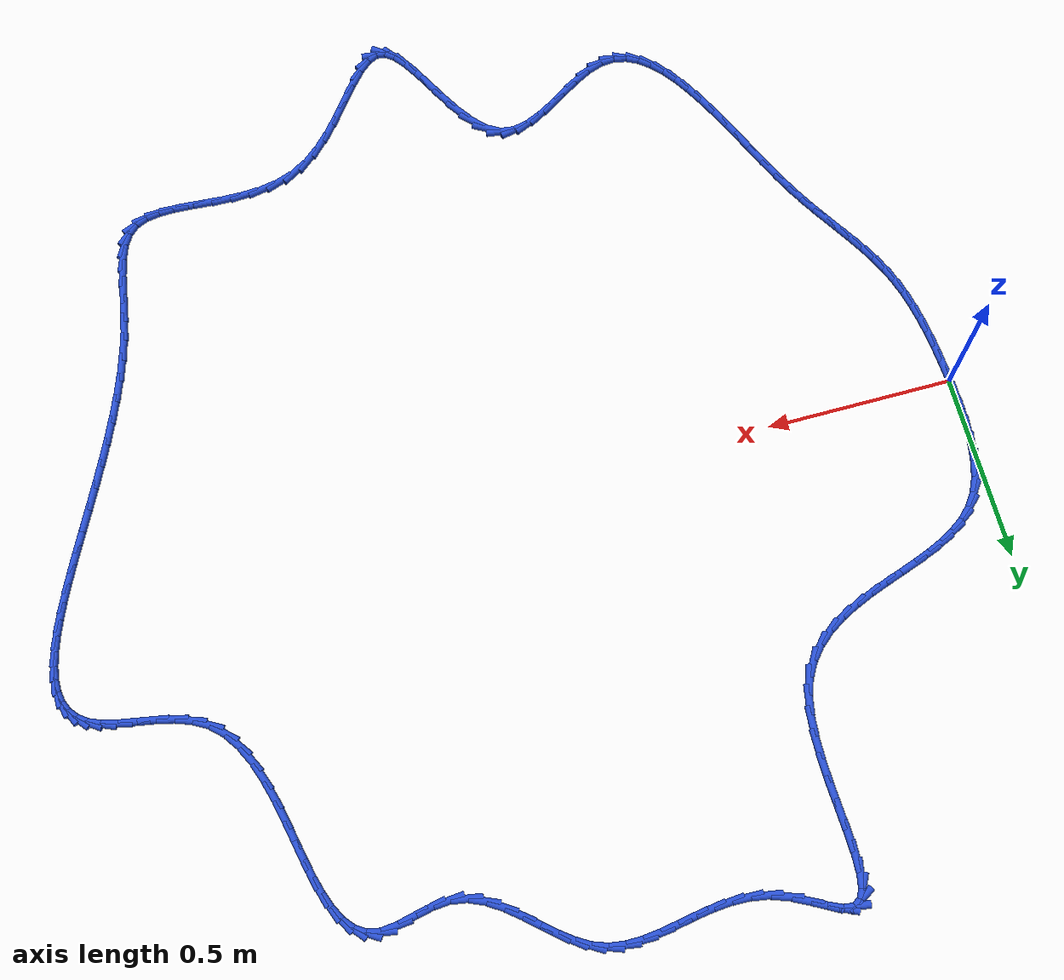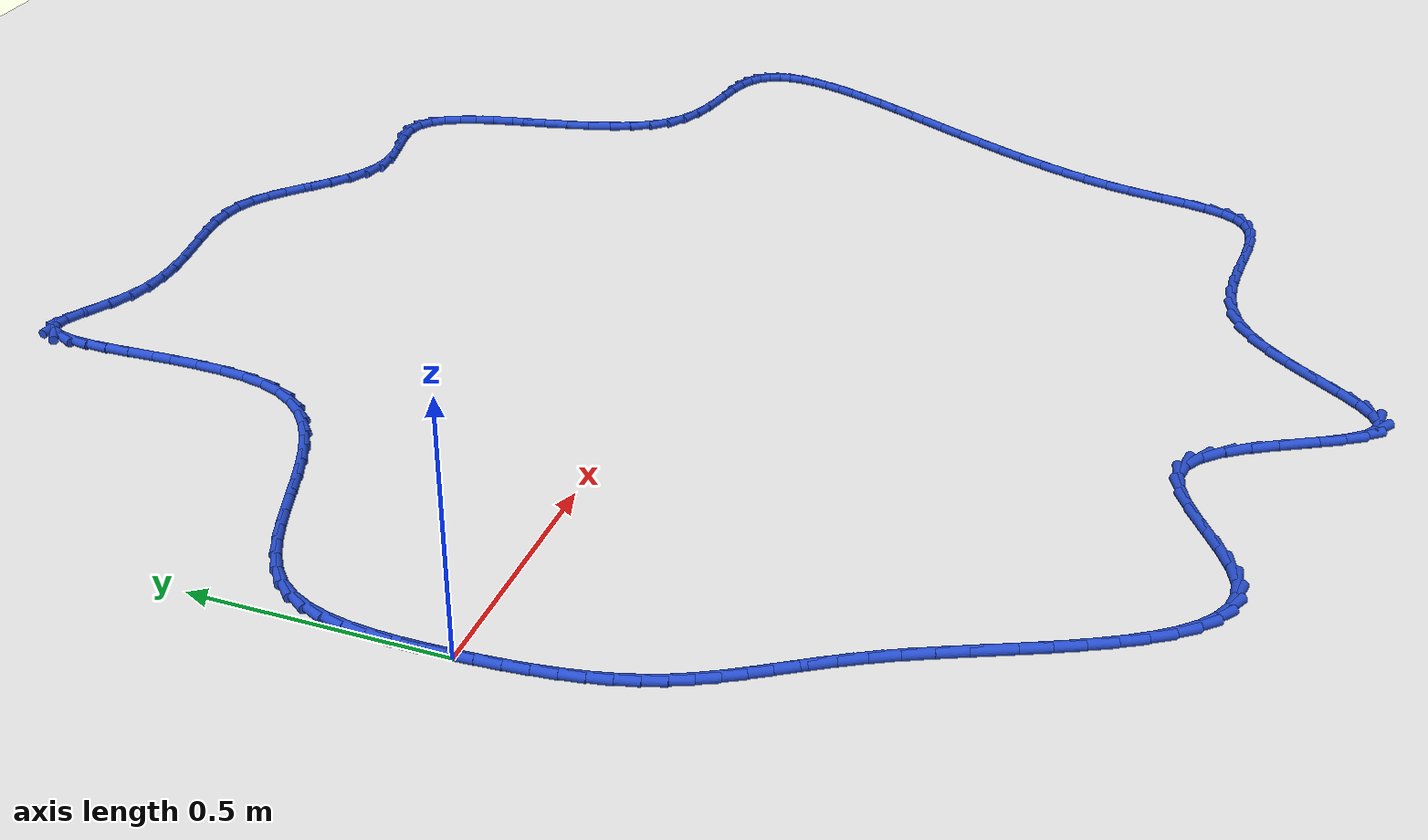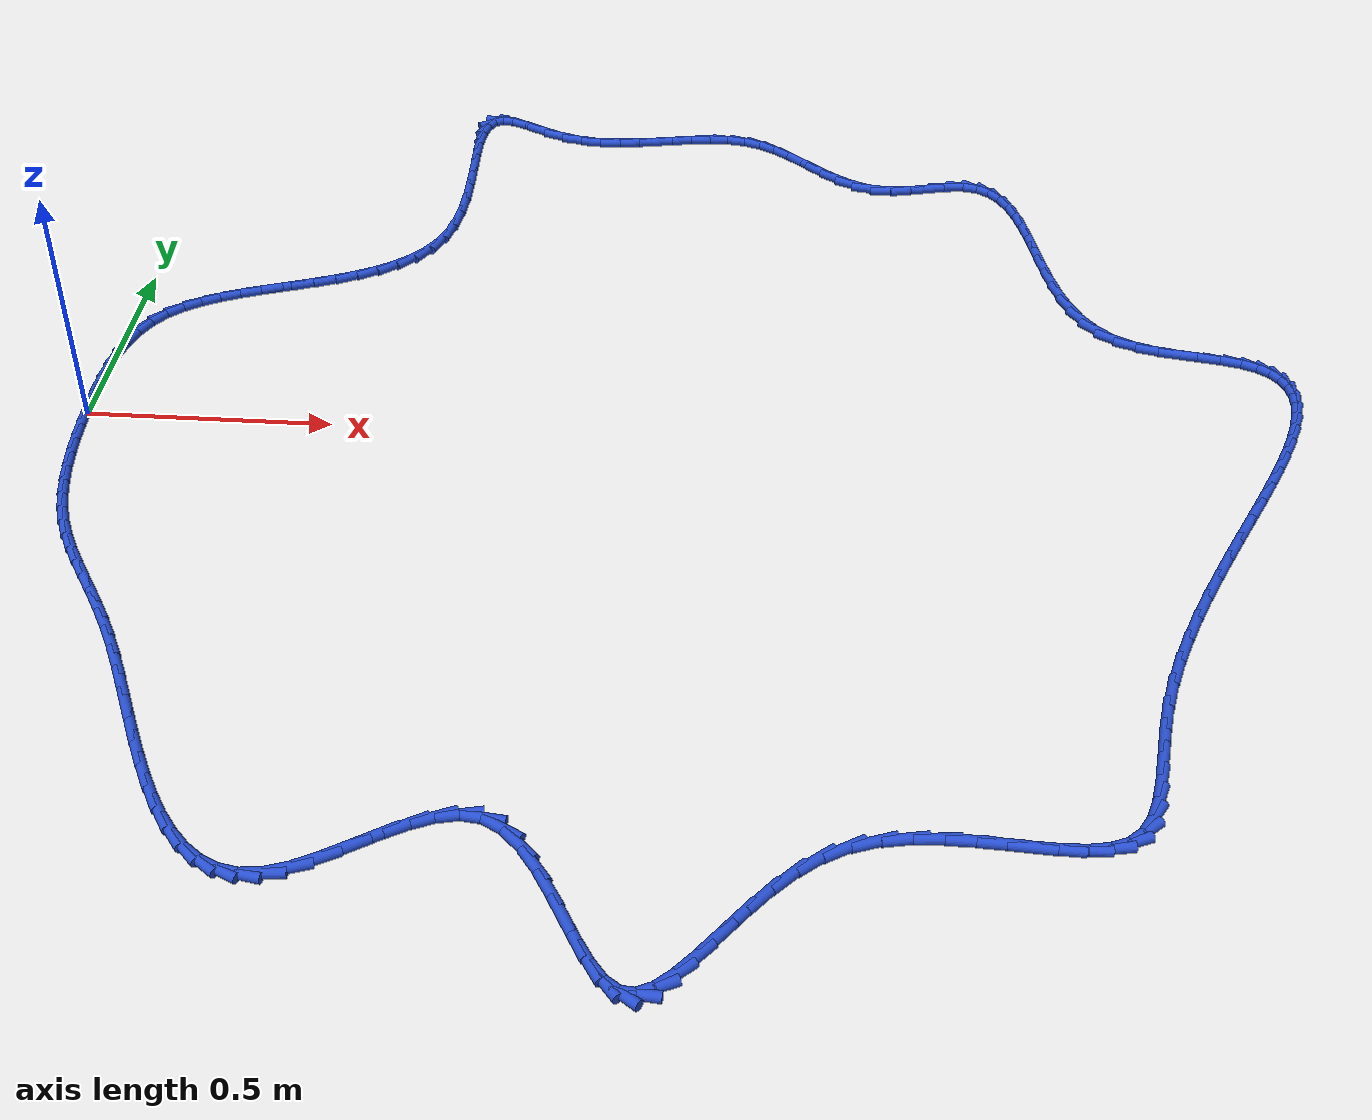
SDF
<sdf version="1.6">
 <world name="default">
  <light name="sun" type="directional">
   <pose>0 0 10 0 -0 0</pose>
   <diffuse>0.8 0.8 0.8 1</diffuse>
   <specular>0.2 0.2 0.2 1</specular>
   <attenuation>
    <range>1000</range>
    <constant>0.9</constant>
    <linear>0.01</linear>
    <quadratic>0.001</quadratic>
   </attenuation>
   <direction>-0.5 0.1 -0.9</direction>
  </light>
  <model name="ground_plane">
   <static>1</static>
   <link name="link">
    <collision name="collision">
     <geometry><plane><normal>0 0 1</normal><size>100 100</size></plane></geometry>
     <surface><friction><ode><mu>100</mu><mu2>50</mu2></ode></friction></surface>
    </collision>
    <visual name="visual">
     <cast_shadows>0</cast_shadows>
     <geometry><plane><normal>0 0 1</normal><size>100 100</size></plane></geometry>
     <material>
      <script><uri>file://media/materials/scripts/gazebo.material</uri><name>Gazebo/WhiteGlow</name></script>
     </material>
    </visual>
   </link>
  </model>
  <gravity>0 0 -9.8</gravity>
  <magnetic_field>6e-06 2.3e-05 -4.2e-05</magnetic_field>
  <atmosphere type="adiabatic"/>
  <physics name="default_physics" default="0" type="ode">
   <max_step_size>0.001</max_step_size>
   <real_time_factor>1</real_time_factor>
   <real_time_update_rate>1000</real_time_update_rate>
  </physics>
  <scene><ambient>0.4 0.4 0.4 1</ambient><background>0.7 0.7 0.7 1</background><shadows>1</shadows></scene>
  <spherical_coordinates>
   <surface_model>EARTH_WGS84</surface_model>
   <latitude_deg>0</latitude_deg>
   <longitude_deg>0</longitude_deg>
   <elevation>0</elevation>
   <heading_deg>0</heading_deg>
  </spherical_coordinates>
  <model name="line">
   <link name="link_0">
    <pose>-2.325613659981407e-17 -9.71445146547012e-17 0.01 0 1.57 -1.5345342746365358</pose>
    <collision name="collision">
     <geometry><cylinder><radius>0.01</radius><length>0.08</length></cylinder></geometry>
    </collision>
    <visual name="visual">
     <material>
      <script><name>Gazebo/Blue</name><uri>file://media/materials/scripts/gazebo.material</uri></script>
     </material>
     <geometry><cylinder><radius>0.01</radius><length>0.08</length></cylinder></geometry>
    </visual>
   </link>
   <link name="link_1">
    <pose>-0.0017730698657499131 0.04887458194099907 0.01 0 1.57 -1.564282334503172</pose>
    <collision name="collision">
     <geometry><cylinder><radius>0.01</radius><length>0.08</length></cylinder></geometry>
    </collision>
    <visual name="visual">
     <material>
      <script><name>Gazebo/Blue</name><uri>file://media/materials/scripts/gazebo.material</uri></script>
     </material>
     <geometry><cylinder><radius>0.01</radius><length>0.08</length></cylinder></geometry>
    </visual>
   </link>
   <link name="link_2">
    <pose>-0.002092094714657815 0.09784920799371946 0.01 0 1.57 1.532465089876885</pose>
    <collision name="collision">
     <geometry><cylinder><radius>0.01</radius><length>0.08</length></cylinder></geometry>
    </collision>
    <visual name="visual">
     <material>
      <script><name>Gazebo/Blue</name><uri>file://media/materials/scripts/gazebo.material</uri></script>
     </material>
     <geometry><cylinder><radius>0.01</radius><length>0.08</length></cylinder></geometry>
    </visual>
   </link>
   <link name="link_3">
    <pose>-0.0002402795984857123 0.14613640738703232 0.01 0 1.57 1.4698964536522816</pose>
    <collision name="collision">
     <geometry><cylinder><radius>0.01</radius><length>0.08</length></cylinder></geometry>
    </collision>
    <visual name="visual">
     <material>
      <script><name>Gazebo/Blue</name><uri>file://media/materials/scripts/gazebo.material</uri></script>
     </material>
     <geometry><cylinder><radius>0.01</radius><length>0.08</length></cylinder></geometry>
    </visual>
   </link>
   <link name="link_4">
    <pose>0.004499170431004423 0.19294870934980896 0.01 0 1.57 1.3856485894613713</pose>
    <collision name="collision">
     <geometry><cylinder><radius>0.01</radius><length>0.08</length></cylinder></geometry>
    </collision>
    <visual name="visual">
     <material>
      <script><name>Gazebo/Blue</name><uri>file://media/materials/scripts/gazebo.material</uri></script>
     </material>
     <geometry><cylinder><radius>0.01</radius><length>0.08</length></cylinder></geometry>
    </visual>
   </link>
   <link name="link_5">
    <pose>0.012843050322050607 0.23749864311092053 0.01 0 1.57 1.2745917084094178</pose>
    <collision name="collision">
     <geometry><cylinder><radius>0.01</radius><length>0.08</length></cylinder></geometry>
    </collision>
    <visual name="visual">
     <material>
      <script><name>Gazebo/Blue</name><uri>file://media/materials/scripts/gazebo.material</uri></script>
     </material>
     <geometry><cylinder><radius>0.01</radius><length>0.08</length></cylinder></geometry>
    </visual>
   </link>
   <link name="link_6">
    <pose>0.025508155022890854 0.27899873789923846 0.01 0 1.57 1.1314003074158698</pose>
    <collision name="collision">
     <geometry><cylinder><radius>0.01</radius><length>0.08</length></cylinder></geometry>
    </collision>
    <visual name="visual">
     <material>
      <script><name>Gazebo/Blue</name><uri>file://media/materials/scripts/gazebo.material</uri></script>
     </material>
     <geometry><cylinder><radius>0.01</radius><length>0.08</length></cylinder></geometry>
    </visual>
   </link>
   <link name="link_7">
    <pose>0.0432112794817632 0.3166615229436339 0.01 0 1.57 0.9535133175750906</pose>
    <collision name="collision">
     <geometry><cylinder><radius>0.01</radius><length>0.08</length></cylinder></geometry>
    </collision>
    <visual name="visual">
     <material>
      <script><name>Gazebo/Blue</name><uri>file://media/materials/scripts/gazebo.material</uri></script>
     </material>
     <geometry><cylinder><radius>0.01</radius><length>0.08</length></cylinder></geometry>
    </visual>
   </link>
   <link name="link_8">
    <pose>0.06666508117431777 0.34970364724908787 0.01 0 1.57 0.7637369404351307</pose>
    <collision name="collision">
     <geometry><cylinder><radius>0.01</radius><length>0.08</length></cylinder></geometry>
    </collision>
    <visual name="visual">
     <material>
      <script><name>Gazebo/Blue</name><uri>file://media/materials/scripts/gazebo.material</uri></script>
     </material>
     <geometry><cylinder><radius>0.01</radius><length>0.08</length></cylinder></geometry>
    </visual>
   </link>
   <link name="link_9">
    <pose>0.0960650317192045 0.377856733610171 0.01 0 1.57 0.6075145350101361</pose>
    <collision name="collision">
     <geometry><cylinder><radius>0.01</radius><length>0.08</length></cylinder></geometry>
    </collision>
    <visual name="visual">
     <material>
      <script><name>Gazebo/Blue</name><uri>file://media/materials/scripts/gazebo.material</uri></script>
     </material>
     <geometry><cylinder><radius>0.01</radius><length>0.08</length></cylinder></geometry>
    </visual>
   </link>
   <link name="link_10">
    <pose>0.13059312312173357 0.40186154965805326 0.01 0 1.57 0.49123489484391397</pose>
    <collision name="collision">
     <geometry><cylinder><radius>0.01</radius><length>0.08</length></cylinder></geometry>
    </collision>
    <visual name="visual">
     <material>
      <script><name>Gazebo/Blue</name><uri>file://media/materials/scripts/gazebo.material</uri></script>
     </material>
     <geometry><cylinder><radius>0.01</radius><length>0.08</length></cylinder></geometry>
    </visual>
   </link>
   <link name="link_11">
    <pose>0.16931363514230593 0.42257607179909024 0.01 0 1.57 0.4107531212111513</pose>
    <collision name="collision">
     <geometry><cylinder><radius>0.01</radius><length>0.08</length></cylinder></geometry>
    </collision>
    <visual name="visual">
     <material>
      <script><name>Gazebo/Blue</name><uri>file://media/materials/scripts/gazebo.material</uri></script>
     </material>
     <geometry><cylinder><radius>0.01</radius><length>0.08</length></cylinder></geometry>
    </visual>
   </link>
   <link name="link_12">
    <pose>0.21129084754132257 0.4408582764396364 0.01 0 1.57 0.36067008310193</pose>
    <collision name="collision">
     <geometry><cylinder><radius>0.01</radius><length>0.08</length></cylinder></geometry>
    </collision>
    <visual name="visual">
     <material>
      <script><name>Gazebo/Blue</name><uri>file://media/materials/scripts/gazebo.material</uri></script>
     </material>
     <geometry><cylinder><radius>0.01</radius><length>0.08</length></cylinder></geometry>
    </visual>
   </link>
   <link name="link_13">
    <pose>0.2555890400791845 0.45756613998604706 0.01 0 1.57 0.33671948561787396</pose>
    <collision name="collision">
     <geometry><cylinder><radius>0.01</radius><length>0.08</length></cylinder></geometry>
    </collision>
    <visual name="visual">
     <material>
      <script><name>Gazebo/Blue</name><uri>file://media/materials/scripts/gazebo.material</uri></script>
     </material>
     <geometry><cylinder><radius>0.01</radius><length>0.08</length></cylinder></geometry>
    </visual>
   </link>
   <link name="link_14">
    <pose>0.30127249251629246 0.47355763884467705 0.01 0 1.57 0.336415322184343</pose>
    <collision name="collision">
     <geometry><cylinder><radius>0.01</radius><length>0.08</length></cylinder></geometry>
    </collision>
    <visual name="visual">
     <material>
      <script><name>Gazebo/Blue</name><uri>file://media/materials/scripts/gazebo.material</uri></script>
     </material>
     <geometry><cylinder><radius>0.01</radius><length>0.08</length></cylinder></geometry>
    </visual>
   </link>
   <link name="link_15">
    <pose>0.34740548461304777 0.4896907494218819 0.01 0 1.57 0.35906150809012216</pose>
    <collision name="collision">
     <geometry><cylinder><radius>0.01</radius><length>0.08</length></cylinder></geometry>
    </collision>
    <visual name="visual">
     <material>
      <script><name>Gazebo/Blue</name><uri>file://media/materials/scripts/gazebo.material</uri></script>
     </material>
     <geometry><cylinder><radius>0.01</radius><length>0.08</length></cylinder></geometry>
    </visual>
   </link>
   <link name="link_16">
    <pose>0.393052296129851 0.5068234481240161 0.01 0 1.57 0.4055932291763059</pose>
    <collision name="collision">
     <geometry><cylinder><radius>0.01</radius><length>0.08</length></cylinder></geometry>
    </collision>
    <visual name="visual">
     <material>
      <script><name>Gazebo/Blue</name><uri>file://media/materials/scripts/gazebo.material</uri></script>
     </material>
     <geometry><cylinder><radius>0.01</radius><length>0.08</length></cylinder></geometry>
    </visual>
   </link>
   <link name="link_17">
    <pose>0.4372772068271033 0.525813711357435 0.01 0 1.57 0.47829293027772085</pose>
    <collision name="collision">
     <geometry><cylinder><radius>0.01</radius><length>0.08</length></cylinder></geometry>
    </collision>
    <visual name="visual">
     <material>
      <script><name>Gazebo/Blue</name><uri>file://media/materials/scripts/gazebo.material</uri></script>
     </material>
     <geometry><cylinder><radius>0.01</radius><length>0.08</length></cylinder></geometry>
    </visual>
   </link>
   <link name="link_18">
    <pose>0.47914449646520585 0.5475195155284938 0.01 0 1.57 0.580124920172925</pose>
    <collision name="collision">
     <geometry><cylinder><radius>0.01</radius><length>0.08</length></cylinder></geometry>
    </collision>
    <visual name="visual">
     <material>
      <script><name>Gazebo/Blue</name><uri>file://media/materials/scripts/gazebo.material</uri></script>
     </material>
     <geometry><cylinder><radius>0.01</radius><length>0.08</length></cylinder></geometry>
    </visual>
   </link>
   <link name="link_19">
    <pose>0.5177184448045593 0.5727988370435471 0.01 0 1.57 0.713179575315378</pose>
    <collision name="collision">
     <geometry><cylinder><radius>0.01</radius><length>0.08</length></cylinder></geometry>
    </collision>
    <visual name="visual">
     <material>
      <script><name>Gazebo/Blue</name><uri>file://media/materials/scripts/gazebo.material</uri></script>
     </material>
     <geometry><cylinder><radius>0.01</radius><length>0.08</length></cylinder></geometry>
    </visual>
   </link>
   <link name="link_20">
    <pose>0.5520633316055646 0.6025096523089503 0.01 0 1.57 0.875835509073799</pose>
    <collision name="collision">
     <geometry><cylinder><radius>0.01</radius><length>0.08</length></cylinder></geometry>
    </collision>
    <visual name="visual">
     <material>
      <script><name>Gazebo/Blue</name><uri>file://media/materials/scripts/gazebo.material</uri></script>
     </material>
     <geometry><cylinder><radius>0.01</radius><length>0.08</length></cylinder></geometry>
    </visual>
   </link>
   <link name="link_21">
    <pose>0.581243436628623 0.6375099377310585 0.01 0 1.57 1.0596260830529012</pose>
    <collision name="collision">
     <geometry><cylinder><radius>0.01</radius><length>0.08</length></cylinder></geometry>
    </collision>
    <visual name="visual">
     <material>
      <script><name>Gazebo/Blue</name><uri>file://media/materials/scripts/gazebo.material</uri></script>
     </material>
     <geometry><cylinder><radius>0.01</radius><length>0.08</length></cylinder></geometry>
    </visual>
   </link>
   <link name="link_22">
    <pose>0.6043230396341355 0.6786576697162265 0.01 0 1.57 1.2462180185621325</pose>
    <collision name="collision">
     <geometry><cylinder><radius>0.01</radius><length>0.08</length></cylinder></geometry>
    </collision>
    <visual name="visual">
     <material>
      <script><name>Gazebo/Blue</name><uri>file://media/materials/scripts/gazebo.material</uri></script>
     </material>
     <geometry><cylinder><radius>0.01</radius><length>0.08</length></cylinder></geometry>
    </visual>
   </link>
   <link name="link_23">
    <pose>0.6204798092887424 0.7266749469851748 0.01 0 1.57 1.3927947746525366</pose>
    <collision name="collision">
     <geometry><cylinder><radius>0.01</radius><length>0.08</length></cylinder></geometry>
    </collision>
    <visual name="visual">
     <material>
      <script><name>Gazebo/Blue</name><uri>file://media/materials/scripts/gazebo.material</uri></script>
     </material>
     <geometry><cylinder><radius>0.01</radius><length>0.08</length></cylinder></geometry>
    </visual>
   </link>
   <link name="link_24">
    <pose>0.6302016903049258 0.7807137210320978 0.01 0 1.57 1.4916448156838837</pose>
    <collision name="collision">
     <geometry><cylinder><radius>0.01</radius><length>0.08</length></cylinder></geometry>
    </collision>
    <visual name="visual">
     <material>
      <script><name>Gazebo/Blue</name><uri>file://media/materials/scripts/gazebo.material</uri></script>
     </material>
     <geometry><cylinder><radius>0.01</radius><length>0.08</length></cylinder></geometry>
    </visual>
   </link>
   <link name="link_25">
    <pose>0.6348182447475353 0.8389174053749285 0.01 0 1.57 1.5566697356535688</pose>
    <collision name="collision">
     <geometry><cylinder><radius>0.01</radius><length>0.08</length></cylinder></geometry>
    </collision>
    <visual name="visual">
     <material>
      <script><name>Gazebo/Blue</name><uri>file://media/materials/scripts/gazebo.material</uri></script>
     </material>
     <geometry><cylinder><radius>0.01</radius><length>0.08</length></cylinder></geometry>
    </visual>
   </link>
   <link name="link_26">
    <pose>0.6356728953595999 0.8994128038214018 0.01 0 1.57 -1.5451291700079521</pose>
    <collision name="collision">
     <geometry><cylinder><radius>0.01</radius><length>0.08</length></cylinder></geometry>
    </collision>
    <visual name="visual">
     <material>
      <script><name>Gazebo/Blue</name><uri>file://media/materials/scripts/gazebo.material</uri></script>
     </material>
     <geometry><cylinder><radius>0.01</radius><length>0.08</length></cylinder></geometry>
    </visual>
   </link>
   <link name="link_27">
    <pose>0.6341090648841485 0.9603267201792515 0.01 0 1.57 -1.5264439548182875</pose>
    <collision name="collision">
     <geometry><cylinder><radius>0.01</radius><length>0.08</length></cylinder></geometry>
    </collision>
    <visual name="visual">
     <material>
      <script><name>Gazebo/Blue</name><uri>file://media/materials/scripts/gazebo.material</uri></script>
     </material>
     <geometry><cylinder><radius>0.01</radius><length>0.08</length></cylinder></geometry>
    </visual>
   </link>
   <link name="link_28">
    <pose>0.6314701760642102 1.0197859582562128 0.01 0 1.57 -1.5285896800313323</pose>
    <collision name="collision">
     <geometry><cylinder><radius>0.01</radius><length>0.08</length></cylinder></geometry>
    </collision>
    <visual name="visual">
     <material>
      <script><name>Gazebo/Blue</name><uri>file://media/materials/scripts/gazebo.material</uri></script>
     </material>
     <geometry><cylinder><radius>0.01</radius><length>0.08</length></cylinder></geometry>
    </visual>
   </link>
   <link name="link_29">
    <pose>0.6290996516428138 1.07591732186002 0.01 0 1.57 -1.5558998651254214</pose>
    <collision name="collision">
     <geometry><cylinder><radius>0.01</radius><length>0.08</length></cylinder></geometry>
    </collision>
    <visual name="visual">
     <material>
      <script><name>Gazebo/Blue</name><uri>file://media/materials/scripts/gazebo.material</uri></script>
     </material>
     <geometry><cylinder><radius>0.01</radius><length>0.08</length></cylinder></geometry>
    </visual>
   </link>
   <link name="link_30">
    <pose>0.6283409143629883 1.1268476147984074 0.01 0 1.57 1.5207544276093539</pose>
    <collision name="collision">
     <geometry><cylinder><radius>0.01</radius><length>0.08</length></cylinder></geometry>
    </collision>
    <visual name="visual">
     <material>
      <script><name>Gazebo/Blue</name><uri>file://media/materials/scripts/gazebo.material</uri></script>
     </material>
     <geometry><cylinder><radius>0.01</radius><length>0.08</length></cylinder></geometry>
    </visual>
   </link>
   <link name="link_31">
    <pose>0.630537386967763 1.1707036408791096 0.01 0 1.57 1.386839334936337</pose>
    <collision name="collision">
     <geometry><cylinder><radius>0.01</radius><length>0.08</length></cylinder></geometry>
    </collision>
    <visual name="visual">
     <material>
      <script><name>Gazebo/Blue</name><uri>file://media/materials/scripts/gazebo.material</uri></script>
     </material>
     <geometry><cylinder><radius>0.01</radius><length>0.08</length></cylinder></geometry>
    </visual>
   </link>
   <link name="link_32">
    <pose>0.6370324922001667 1.2056122039098618 0.01 0 1.57 1.1040578928921694</pose>
    <collision name="collision">
     <geometry><cylinder><radius>0.01</radius><length>0.08</length></cylinder></geometry>
    </collision>
    <visual name="visual">
     <material>
      <script><name>Gazebo/Blue</name><uri>file://media/materials/scripts/gazebo.material</uri></script>
     </material>
     <geometry><cylinder><radius>0.01</radius><length>0.08</length></cylinder></geometry>
    </visual>
   </link>
   <link name="link_33">
    <pose>0.6491696528032284 1.2297001076983973 0.01 0 1.57 0.5373556526796155</pose>
    <collision name="collision">
     <geometry><cylinder><radius>0.01</radius><length>0.08</length></cylinder></geometry>
    </collision>
    <visual name="visual">
     <material>
      <script><name>Gazebo/Blue</name><uri>file://media/materials/scripts/gazebo.material</uri></script>
     </material>
     <geometry><cylinder><radius>0.01</radius><length>0.08</length></cylinder></geometry>
    </visual>
   </link>
   <link name="link_34">
    <pose>0.6682922915199769 1.2410941560524515 0.01 0 1.57 -0.11305323790939938</pose>
    <collision name="collision">
     <geometry><cylinder><radius>0.01</radius><length>0.08</length></cylinder></geometry>
    </collision>
    <visual name="visual">
     <material>
      <script><name>Gazebo/Blue</name><uri>file://media/materials/scripts/gazebo.material</uri></script>
     </material>
     <geometry><cylinder><radius>0.01</radius><length>0.08</length></cylinder></geometry>
    </visual>
   </link>
   <link name="link_35">
    <pose>0.6957186965011104 1.2379802344676312 0.01 0 1.57 -0.425298309428842</pose>
    <collision name="collision">
     <geometry><cylinder><radius>0.01</radius><length>0.08</length></cylinder></geometry>
    </collision>
    <visual name="visual">
     <material>
      <script><name>Gazebo/Blue</name><uri>file://media/materials/scripts/gazebo.material</uri></script>
     </material>
     <geometry><cylinder><radius>0.01</radius><length>0.08</length></cylinder></geometry>
    </visual>
   </link>
   <link name="link_36">
    <pose>0.7313679768481677 1.221833156255417 0.01 0 1.57 -0.49959470110784243</pose>
    <collision name="collision">
     <geometry><cylinder><radius>0.01</radius><length>0.08</length></cylinder></geometry>
    </collision>
    <visual name="visual">
     <material>
      <script><name>Gazebo/Blue</name><uri>file://media/materials/scripts/gazebo.material</uri></script>
     </material>
     <geometry><cylinder><radius>0.01</radius><length>0.08</length></cylinder></geometry>
    </visual>
   </link>
   <link name="link_37">
    <pose>0.7730509146086263 1.199083594734797 0.01 0 1.57 -0.46072907651925005</pose>
    <collision name="collision">
     <geometry><cylinder><radius>0.01</radius><length>0.08</length></cylinder></geometry>
    </collision>
    <visual name="visual">
     <material>
      <script><name>Gazebo/Blue</name><uri>file://media/materials/scripts/gazebo.material</uri></script>
     </material>
     <geometry><cylinder><radius>0.01</radius><length>0.08</length></cylinder></geometry>
    </visual>
   </link>
   <link name="link_38">
    <pose>0.8184038105999125 1.176572360991766 0.01 0 1.57 -0.3255957145227264</pose>
    <collision name="collision">
     <geometry><cylinder><radius>0.01</radius><length>0.08</length></cylinder></geometry>
    </collision>
    <visual name="visual">
     <material>
      <script><name>Gazebo/Blue</name><uri>file://media/materials/scripts/gazebo.material</uri></script>
     </material>
     <geometry><cylinder><radius>0.01</radius><length>0.08</length></cylinder></geometry>
    </visual>
   </link>
   <link name="link_39">
    <pose>0.8651486734777377 1.1607907699826252 0.01 0 1.57 -0.15506147269671045</pose>
    <collision name="collision">
     <geometry><cylinder><radius>0.01</radius><length>0.08</length></cylinder></geometry>
    </collision>
    <visual name="visual">
     <material>
      <script><name>Gazebo/Blue</name><uri>file://media/materials/scripts/gazebo.material</uri></script>
     </material>
     <geometry><cylinder><radius>0.01</radius><length>0.08</length></cylinder></geometry>
    </visual>
   </link>
   <link name="link_40">
    <pose>0.9121825509090812 1.1534386077336247 0.01 0 1.57 -0.01486051827643493</pose>
    <collision name="collision">
     <geometry><cylinder><radius>0.01</radius><length>0.08</length></cylinder></geometry>
    </collision>
    <visual name="visual">
     <material>
      <script><name>Gazebo/Blue</name><uri>file://media/materials/scripts/gazebo.material</uri></script>
     </material>
     <geometry><cylinder><radius>0.01</radius><length>0.08</length></cylinder></geometry>
    </visual>
   </link>
   <link name="link_41">
    <pose>0.9592550725568714 1.1527390341678247 0.01 0 1.57 0.08719682032494049</pose>
    <collision name="collision">
     <geometry><cylinder><radius>0.01</radius><length>0.08</length></cylinder></geometry>
    </collision>
    <visual name="visual">
     <material>
      <script><name>Gazebo/Blue</name><uri>file://media/materials/scripts/gazebo.material</uri></script>
     </material>
     <geometry><cylinder><radius>0.01</radius><length>0.08</length></cylinder></geometry>
    </visual>
   </link>
   <link name="link_42">
    <pose>1.0061349969377271 1.1568372063037295 0.01 0 1.57 0.15041927867017058</pose>
    <collision name="collision">
     <geometry><cylinder><radius>0.01</radius><length>0.08</length></cylinder></geometry>
    </collision>
    <visual name="visual">
     <material>
      <script><name>Gazebo/Blue</name><uri>file://media/materials/scripts/gazebo.material</uri></script>
     </material>
     <geometry><cylinder><radius>0.01</radius><length>0.08</length></cylinder></geometry>
    </visual>
   </link>
   <link name="link_43">
    <pose>1.0525910825682656 1.1638782811598427 0.01 0 1.57 0.17565883316639536</pose>
    <collision name="collision">
     <geometry><cylinder><radius>0.01</radius><length>0.08</length></cylinder></geometry>
    </collision>
    <visual name="visual">
     <material>
      <script><name>Gazebo/Blue</name><uri>file://media/materials/scripts/gazebo.material</uri></script>
     </material>
     <geometry><cylinder><radius>0.01</radius><length>0.08</length></cylinder></geometry>
    </visual>
   </link>
   <link name="link_44">
    <pose>1.0983920879651046 1.1720074157546685 0.01 0 1.57 0.16247368161127423</pose>
    <collision name="collision">
     <geometry><cylinder><radius>0.01</radius><length>0.08</length></cylinder></geometry>
    </collision>
    <visual name="visual">
     <material>
      <script><name>Gazebo/Blue</name><uri>file://media/materials/scripts/gazebo.material</uri></script>
     </material>
     <geometry><cylinder><radius>0.01</radius><length>0.08</length></cylinder></geometry>
    </visual>
   </link>
   <link name="link_45">
    <pose>1.143306771644862 1.1793697671067105 0.01 0 1.57 0.10782305388927933</pose>
    <collision name="collision">
     <geometry><cylinder><radius>0.01</radius><length>0.08</length></cylinder></geometry>
    </collision>
    <visual name="visual">
     <material>
      <script><name>Gazebo/Blue</name><uri>file://media/materials/scripts/gazebo.material</uri></script>
     </material>
     <geometry><cylinder><radius>0.01</radius><length>0.08</length></cylinder></geometry>
    </visual>
   </link>
   <link name="link_46">
    <pose>1.1871038921241555 1.1841104922344723 0.01 0 1.57 0.006225276630199771</pose>
    <collision name="collision">
     <geometry><cylinder><radius>0.01</radius><length>0.08</length></cylinder></geometry>
    </collision>
    <visual name="visual">
     <material>
      <script><name>Gazebo/Blue</name><uri>file://media/materials/scripts/gazebo.material</uri></script>
     </material>
     <geometry><cylinder><radius>0.01</radius><length>0.08</length></cylinder></geometry>
    </visual>
   </link>
   <link name="link_47">
    <pose>1.2295522079196026 1.184374748156458 0.01 0 1.57 -0.14737758142121188</pose>
    <collision name="collision">
     <geometry><cylinder><radius>0.01</radius><length>0.08</length></cylinder></geometry>
    </collision>
    <visual name="visual">
     <material>
      <script><name>Gazebo/Blue</name><uri>file://media/materials/scripts/gazebo.material</uri></script>
     </material>
     <geometry><cylinder><radius>0.01</radius><length>0.08</length></cylinder></geometry>
    </visual>
   </link>
   <link name="link_48">
    <pose>1.2704204775478212 1.178307691891171 0.01 0 1.57 -0.3490148421377518</pose>
    <collision name="collision">
     <geometry><cylinder><radius>0.01</radius><length>0.08</length></cylinder></geometry>
    </collision>
    <visual name="visual">
     <material>
      <script><name>Gazebo/Blue</name><uri>file://media/materials/scripts/gazebo.material</uri></script>
     </material>
     <geometry><cylinder><radius>0.01</radius><length>0.08</length></cylinder></geometry>
    </visual>
   </link>
   <link name="link_49">
    <pose>1.3094846104290145 1.1640917668140862 0.01 0 1.57 -0.5401410061688547</pose>
    <collision name="collision">
     <geometry><cylinder><radius>0.01</radius><length>0.08</length></cylinder></geometry>
    </collision>
    <visual name="visual">
     <material>
      <script><name>Gazebo/Blue</name><uri>file://media/materials/scripts/gazebo.material</uri></script>
     </material>
     <geometry><cylinder><radius>0.01</radius><length>0.08</length></cylinder></geometry>
    </visual>
   </link>
   <link name="link_50">
    <pose>1.346860193910875 1.1416805704364865 0.01 0 1.57 -0.6597737508399606</pose>
    <collision name="collision">
     <geometry><cylinder><radius>0.01</radius><length>0.08</length></cylinder></geometry>
    </collision>
    <visual name="visual">
     <material>
      <script><name>Gazebo/Blue</name><uri>file://media/materials/scripts/gazebo.material</uri></script>
     </material>
     <geometry><cylinder><radius>0.01</radius><length>0.08</length></cylinder></geometry>
    </visual>
   </link>
   <link name="link_51">
    <pose>1.3831434959504354 1.1135340728665575 0.01 0 1.57 -0.7170275605148184</pose>
    <collision name="collision">
     <geometry><cylinder><radius>0.01</radius><length>0.08</length></cylinder></geometry>
    </collision>
    <visual name="visual">
     <material>
      <script><name>Gazebo/Blue</name><uri>file://media/materials/scripts/gazebo.material</uri></script>
     </material>
     <geometry><cylinder><radius>0.01</radius><length>0.08</length></cylinder></geometry>
    </visual>
   </link>
   <link name="link_52">
    <pose>1.4189672059867677 1.0823021536923914 0.01 0 1.57 -0.7215025059016286</pose>
    <collision name="collision">
     <geometry><cylinder><radius>0.01</radius><length>0.08</length></cylinder></geometry>
    </collision>
    <visual name="visual">
     <material>
      <script><name>Gazebo/Blue</name><uri>file://media/materials/scripts/gazebo.material</uri></script>
     </material>
     <geometry><cylinder><radius>0.01</radius><length>0.08</length></cylinder></geometry>
    </visual>
   </link>
   <link name="link_53">
    <pose>1.4549640134589423 1.0506346925020829 0.01 0 1.57 -0.6749239642312961</pose>
    <collision name="collision">
     <geometry><cylinder><radius>0.01</radius><length>0.08</length></cylinder></geometry>
    </collision>
    <visual name="visual">
     <material>
      <script><name>Gazebo/Blue</name><uri>file://media/materials/scripts/gazebo.material</uri></script>
     </material>
     <geometry><cylinder><radius>0.01</radius><length>0.08</length></cylinder></geometry>
    </visual>
   </link>
   <link name="link_54">
    <pose>1.4917666078060319 1.0211815688837251 0.01 0 1.57 -0.571436669646734</pose>
    <collision name="collision">
     <geometry><cylinder><radius>0.01</radius><length>0.08</length></cylinder></geometry>
    </collision>
    <visual name="visual">
     <material>
      <script><name>Gazebo/Blue</name><uri>file://media/materials/scripts/gazebo.material</uri></script>
     </material>
     <geometry><cylinder><radius>0.01</radius><length>0.08</length></cylinder></geometry>
    </visual>
   </link>
   <link name="link_55">
    <pose>1.530007678467108 0.9965926624254121 0.01 0 1.57 -0.4006536636887486</pose>
    <collision name="collision">
     <geometry><cylinder><radius>0.01</radius><length>0.08</length></cylinder></geometry>
    </collision>
    <visual name="visual">
     <material>
      <script><name>Gazebo/Blue</name><uri>file://media/materials/scripts/gazebo.material</uri></script>
     </material>
     <geometry><cylinder><radius>0.01</radius><length>0.08</length></cylinder></geometry>
    </visual>
   </link>
   <link name="link_56">
    <pose>1.570319914881242 0.9795178527152377 0.01 0 1.57 -0.1593014714374803</pose>
    <collision name="collision">
     <geometry><cylinder><radius>0.01</radius><length>0.08</length></cylinder></geometry>
    </collision>
    <visual name="visual">
     <material>
      <script><name>Gazebo/Blue</name><uri>file://media/materials/scripts/gazebo.material</uri></script>
     </material>
     <geometry><cylinder><radius>0.01</radius><length>0.08</length></cylinder></geometry>
    </visual>
   </link>
   <link name="link_57">
    <pose>1.6133359211253027 0.9726067798111606 0.01 0 1.57 0.09118167925828746</pose>
    <collision name="collision">
     <geometry><cylinder><radius>0.01</radius><length>0.08</length></cylinder></geometry>
    </collision>
    <visual name="visual">
     <material>
      <script><name>Gazebo/Blue</name><uri>file://media/materials/scripts/gazebo.material</uri></script>
     </material>
     <geometry><cylinder><radius>0.01</radius><length>0.08</length></cylinder></geometry>
    </visual>
   </link>
   <link name="link_58">
    <pose>1.65907529817504 0.9767889698282126 0.01 0 1.57 0.2197144508960467</pose>
    <collision name="collision">
     <geometry><cylinder><radius>0.01</radius><length>0.08</length></cylinder></geometry>
    </collision>
    <visual name="visual">
     <material>
      <script><name>Gazebo/Blue</name><uri>file://media/materials/scripts/gazebo.material</uri></script>
     </material>
     <geometry><cylinder><radius>0.01</radius><length>0.08</length></cylinder></geometry>
    </visual>
   </link>
   <link name="link_59">
    <pose>1.705475381158548 0.9871510183792858 0.01 0 1.57 0.22907294432351802</pose>
    <collision name="collision">
     <geometry><cylinder><radius>0.01</radius><length>0.08</length></cylinder></geometry>
    </collision>
    <visual name="visual">
     <material>
      <script><name>Gazebo/Blue</name><uri>file://media/materials/scripts/gazebo.material</uri></script>
     </material>
     <geometry><cylinder><radius>0.01</radius><length>0.08</length></cylinder></geometry>
    </visual>
   </link>
   <link name="link_60">
    <pose>1.7500317883702818 0.9975400440126677 0.01 0 1.57 0.10563113398468948</pose>
    <collision name="collision">
     <geometry><cylinder><radius>0.01</radius><length>0.08</length></cylinder></geometry>
    </collision>
    <visual name="visual">
     <material>
      <script><name>Gazebo/Blue</name><uri>file://media/materials/scripts/gazebo.material</uri></script>
     </material>
     <geometry><cylinder><radius>0.01</radius><length>0.08</length></cylinder></geometry>
    </visual>
   </link>
   <link name="link_61">
    <pose>1.7902401381046957 1.001803165276645 0.01 0 1.57 -0.1973960808550893</pose>
    <collision name="collision">
     <geometry><cylinder><radius>0.01</radius><length>0.08</length></cylinder></geometry>
    </collision>
    <visual name="visual">
     <material>
      <script><name>Gazebo/Blue</name><uri>file://media/materials/scripts/gazebo.material</uri></script>
     </material>
     <geometry><cylinder><radius>0.01</radius><length>0.08</length></cylinder></geometry>
    </visual>
   </link>
   <link name="link_62">
    <pose>1.8241523940616622 0.9950206957100494 0.01 0 1.57 -0.5646404480415788</pose>
    <collision name="collision">
     <geometry><cylinder><radius>0.01</radius><length>0.08</length></cylinder></geometry>
    </collision>
    <visual name="visual">
     <material>
      <script><name>Gazebo/Blue</name><uri>file://media/materials/scripts/gazebo.material</uri></script>
     </material>
     <geometry><cylinder><radius>0.01</radius><length>0.08</length></cylinder></geometry>
    </visual>
   </link>
   <link name="link_63">
    <pose>1.8520972349242029 0.9773195143212523 0.01 0 1.57 -0.8713072369716914</pose>
    <collision name="collision">
     <geometry><cylinder><radius>0.01</radius><length>0.08</length></cylinder></geometry>
    </collision>
    <visual name="visual">
     <material>
      <script><name>Gazebo/Blue</name><uri>file://media/materials/scripts/gazebo.material</uri></script>
     </material>
     <geometry><cylinder><radius>0.01</radius><length>0.08</length></cylinder></geometry>
    </visual>
   </link>
   <link name="link_64">
    <pose>1.8749856461086294 0.9501172409775617 0.01 0 1.57 -1.0825195071482632</pose>
    <collision name="collision">
     <geometry><cylinder><radius>0.01</radius><length>0.08</length></cylinder></geometry>
    </collision>
    <visual name="visual">
     <material>
      <script><name>Gazebo/Blue</name><uri>file://media/materials/scripts/gazebo.material</uri></script>
     </material>
     <geometry><cylinder><radius>0.01</radius><length>0.08</length></cylinder></geometry>
    </visual>
   </link>
   <link name="link_65">
    <pose>1.8937286132812754 0.9148314961004854 0.01 0 1.57 -1.2167012003152116</pose>
    <collision name="collision">
     <geometry><cylinder><radius>0.01</radius><length>0.08</length></cylinder></geometry>
    </collision>
    <visual name="visual">
     <material>
      <script><name>Gazebo/Blue</name><uri>file://media/materials/scripts/gazebo.material</uri></script>
     </material>
     <geometry><cylinder><radius>0.01</radius><length>0.08</length></cylinder></geometry>
    </visual>
   </link>
   <link name="link_66">
    <pose>1.909237122108475 0.8728799001115313 0.01 0 1.57 -1.2983950971608522</pose>
    <collision name="collision">
     <geometry><cylinder><radius>0.01</radius><length>0.08</length></cylinder></geometry>
    </collision>
    <visual name="visual">
     <material>
      <script><name>Gazebo/Blue</name><uri>file://media/materials/scripts/gazebo.material</uri></script>
     </material>
     <geometry><cylinder><radius>0.01</radius><length>0.08</length></cylinder></geometry>
    </visual>
   </link>
   <link name="link_67">
    <pose>1.9224221582565633 0.8256800734322086 0.01 0 1.57 -1.3440664227321206</pose>
    <collision name="collision">
     <geometry><cylinder><radius>0.01</radius><length>0.08</length></cylinder></geometry>
    </collision>
    <visual name="visual">
     <material>
      <script><name>Gazebo/Blue</name><uri>file://media/materials/scripts/gazebo.material</uri></script>
     </material>
     <geometry><cylinder><radius>0.01</radius><length>0.08</length></cylinder></geometry>
    </visual>
   </link>
   <link name="link_68">
    <pose>1.9341947073918726 0.7746496364840242 0.01 0 1.57 -1.362945364394207</pose>
    <collision name="collision">
     <geometry><cylinder><radius>0.01</radius><length>0.08</length></cylinder></geometry>
    </collision>
    <visual name="visual">
     <material>
      <script><name>Gazebo/Blue</name><uri>file://media/materials/scripts/gazebo.material</uri></script>
     </material>
     <geometry><cylinder><radius>0.01</radius><length>0.08</length></cylinder></geometry>
    </visual>
   </link>
   <link name="link_69">
    <pose>1.9454657551807395 0.7212062096884863 0.01 0 1.57 -1.3594382358039503</pose>
    <collision name="collision">
     <geometry><cylinder><radius>0.01</radius><length>0.08</length></cylinder></geometry>
    </collision>
    <visual name="visual">
     <material>
      <script><name>Gazebo/Blue</name><uri>file://media/materials/scripts/gazebo.material</uri></script>
     </material>
     <geometry><cylinder><radius>0.01</radius><length>0.08</length></cylinder></geometry>
    </visual>
   </link>
   <link name="link_70">
    <pose>1.957146287289496 0.6667674134671038 0.01 0 1.57 -1.3346032305884994</pose>
    <collision name="collision">
     <geometry><cylinder><radius>0.01</radius><length>0.08</length></cylinder></geometry>
    </collision>
    <visual name="visual">
     <material>
      <script><name>Gazebo/Blue</name><uri>file://media/materials/scripts/gazebo.material</uri></script>
     </material>
     <geometry><cylinder><radius>0.01</radius><length>0.08</length></cylinder></geometry>
    </visual>
   </link>
   <link name="link_71">
    <pose>1.970147289384478 0.6127508682413843 0.01 0 1.57 -1.2867503392354904</pose>
    <collision name="collision">
     <geometry><cylinder><radius>0.01</radius><length>0.08</length></cylinder></geometry>
    </collision>
    <visual name="visual">
     <material>
      <script><name>Gazebo/Blue</name><uri>file://media/materials/scripts/gazebo.material</uri></script>
     </material>
     <geometry><cylinder><radius>0.01</radius><length>0.08</length></cylinder></geometry>
    </visual>
   </link>
   <link name="link_72">
    <pose>1.985379747132019 0.5605741944328366 0.01 0 1.57 -1.2114844282544301</pose>
    <collision name="collision">
     <geometry><cylinder><radius>0.01</radius><length>0.08</length></cylinder></geometry>
    </collision>
    <visual name="visual">
     <material>
      <script><name>Gazebo/Blue</name><uri>file://media/materials/scripts/gazebo.material</uri></script>
     </material>
     <geometry><cylinder><radius>0.01</radius><length>0.08</length></cylinder></geometry>
    </visual>
   </link>
   <link name="link_73">
    <pose>2.003754646198453 0.5116550124629684 0.01 0 1.57 -1.1016258572999107</pose>
    <collision name="collision">
     <geometry><cylinder><radius>0.01</radius><length>0.08</length></cylinder></geometry>
    </collision>
    <visual name="visual">
     <material>
      <script><name>Gazebo/Blue</name><uri>file://media/materials/scripts/gazebo.material</uri></script>
     </material>
     <geometry><cylinder><radius>0.01</radius><length>0.08</length></cylinder></geometry>
    </visual>
   </link>
   <link name="link_74">
    <pose>2.026182972250115 0.46741094275328754 0.01 0 1.57 -0.948090337947648</pose>
    <collision name="collision">
     <geometry><cylinder><radius>0.01</radius><length>0.08</length></cylinder></geometry>
    </collision>
    <visual name="visual">
     <material>
      <script><name>Gazebo/Blue</name><uri>file://media/materials/scripts/gazebo.material</uri></script>
     </material>
     <geometry><cylinder><radius>0.01</radius><length>0.08</length></cylinder></geometry>
    </visual>
   </link>
   <link name="link_75">
    <pose>2.053575710953338 0.4292596057253028 0.01 0 1.57 -0.7443136556620035</pose>
    <collision name="collision">
     <geometry><cylinder><radius>0.01</radius><length>0.08</length></cylinder></geometry>
    </collision>
    <visual name="visual">
     <material>
      <script><name>Gazebo/Blue</name><uri>file://media/materials/scripts/gazebo.material</uri></script>
     </material>
     <geometry><cylinder><radius>0.01</radius><length>0.08</length></cylinder></geometry>
    </visual>
   </link>
   <link name="link_76">
    <pose>2.0868438479744573 0.3986186218005221 0.01 0 1.57 -0.5100212018672339</pose>
    <collision name="collision">
     <geometry><cylinder><radius>0.01</radius><length>0.08</length></cylinder></geometry>
    </collision>
    <visual name="visual">
     <material>
      <script><name>Gazebo/Blue</name><uri>file://media/materials/scripts/gazebo.material</uri></script>
     </material>
     <geometry><cylinder><radius>0.01</radius><length>0.08</length></cylinder></geometry>
    </visual>
   </link>
   <link name="link_77">
    <pose>2.1264797395076647 0.37644683711900007 0.01 0 1.57 -0.329663217718437</pose>
    <collision name="collision">
     <geometry><cylinder><radius>0.01</radius><length>0.08</length></cylinder></geometry>
    </collision>
    <visual name="visual">
     <material>
      <script><name>Gazebo/Blue</name><uri>file://media/materials/scripts/gazebo.material</uri></script>
     </material>
     <geometry><cylinder><radius>0.01</radius><length>0.08</length></cylinder></geometry>
    </visual>
   </link>
   <link name="link_78">
    <pose>2.170774972781658 0.3612912843485565 0.01 0 1.57 -0.21955067635210143</pose>
    <collision name="collision">
     <geometry><cylinder><radius>0.01</radius><length>0.08</length></cylinder></geometry>
    </collision>
    <visual name="visual">
     <material>
      <script><name>Gazebo/Blue</name><uri>file://media/materials/scripts/gazebo.material</uri></script>
     </material>
     <geometry><cylinder><radius>0.01</radius><length>0.08</length></cylinder></geometry>
    </visual>
   </link>
   <link name="link_79">
    <pose>2.217300474067061 0.35090922683780634 0.01 0 1.57 -0.16789260027877784</pose>
    <collision name="collision">
     <geometry><cylinder><radius>0.01</radius><length>0.08</length></cylinder></geometry>
    </collision>
    <visual name="visual">
     <material>
      <script><name>Gazebo/Blue</name><uri>file://media/materials/scripts/gazebo.material</uri></script>
     </material>
     <geometry><cylinder><radius>0.01</radius><length>0.08</length></cylinder></geometry>
    </visual>
   </link>
   <link name="link_80">
    <pose>2.263626754714917 0.34305747322673774 0.01 0 1.57 -0.17141467375027794</pose>
    <collision name="collision">
     <geometry><cylinder><radius>0.01</radius><length>0.08</length></cylinder></geometry>
    </collision>
    <visual name="visual">
     <material>
      <script><name>Gazebo/Blue</name><uri>file://media/materials/scripts/gazebo.material</uri></script>
     </material>
     <geometry><cylinder><radius>0.01</radius><length>0.08</length></cylinder></geometry>
    </visual>
   </link>
   <link name="link_81">
    <pose>2.3073243260762646 0.3354928321553386 0.01 0 1.57 -0.2415870384076508</pose>
    <collision name="collision">
     <geometry><cylinder><radius>0.01</radius><length>0.08</length></cylinder></geometry>
    </collision>
    <visual name="visual">
     <material>
      <script><name>Gazebo/Blue</name><uri>file://media/materials/scripts/gazebo.material</uri></script>
     </material>
     <geometry><cylinder><radius>0.01</radius><length>0.08</length></cylinder></geometry>
    </visual>
   </link>
   <link name="link_82">
    <pose>2.34596369950215 0.32597211226359746 0.01 0 1.57 -0.40150694102356255</pose>
    <collision name="collision">
     <geometry><cylinder><radius>0.01</radius><length>0.08</length></cylinder></geometry>
    </collision>
    <visual name="visual">
     <material>
      <script><name>Gazebo/Blue</name><uri>file://media/materials/scripts/gazebo.material</uri></script>
     </material>
     <geometry><cylinder><radius>0.01</radius><length>0.08</length></cylinder></geometry>
    </visual>
   </link>
   <link name="link_83">
    <pose>2.3775047148390116 0.3125807223928332 0.01 0 1.57 -0.6249965864616291</pose>
    <collision name="collision">
     <geometry><cylinder><radius>0.01</radius><length>0.08</length></cylinder></geometry>
    </collision>
    <visual name="visual">
     <material>
      <script><name>Gazebo/Blue</name><uri>file://media/materials/scripts/gazebo.material</uri></script>
     </material>
     <geometry><cylinder><radius>0.01</radius><length>0.08</length></cylinder></geometry>
    </visual>
   </link>
   <link name="link_84">
    <pose>2.401832296421901 0.29502887706391967 0.01 0 1.57 -0.8850260160110283</pose>
    <collision name="collision">
     <geometry><cylinder><radius>0.01</radius><length>0.08</length></cylinder></geometry>
    </collision>
    <visual name="visual">
     <material>
      <script><name>Gazebo/Blue</name><uri>file://media/materials/scripts/gazebo.material</uri></script>
     </material>
     <geometry><cylinder><radius>0.01</radius><length>0.08</length></cylinder></geometry>
    </visual>
   </link>
   <link name="link_85">
    <pose>2.419425313348821 0.2735280907821698 0.01 0 1.57 -1.148589742444939</pose>
    <collision name="collision">
     <geometry><cylinder><radius>0.01</radius><length>0.08</length></cylinder></geometry>
    </collision>
    <visual name="visual">
     <material>
      <script><name>Gazebo/Blue</name><uri>file://media/materials/scripts/gazebo.material</uri></script>
     </material>
     <geometry><cylinder><radius>0.01</radius><length>0.08</length></cylinder></geometry>
    </visual>
   </link>
   <link name="link_86">
    <pose>2.430762804339405 0.2482900212165841 0.01 0 1.57 -1.3798184031001295</pose>
    <collision name="collision">
     <geometry><cylinder><radius>0.01</radius><length>0.08</length></cylinder></geometry>
    </collision>
    <visual name="visual">
     <material>
      <script><name>Gazebo/Blue</name><uri>file://media/materials/scripts/gazebo.material</uri></script>
     </material>
     <geometry><cylinder><radius>0.01</radius><length>0.08</length></cylinder></geometry>
    </visual>
   </link>
   <link name="link_87">
    <pose>2.436323808113289 0.21952632603616243 0.01 0 1.57 -1.5625803496658572</pose>
    <collision name="collision">
     <geometry><cylinder><radius>0.01</radius><length>0.08</length></cylinder></geometry>
    </collision>
    <visual name="visual">
     <material>
      <script><name>Gazebo/Blue</name><uri>file://media/materials/scripts/gazebo.material</uri></script>
     </material>
     <geometry><cylinder><radius>0.01</radius><length>0.08</length></cylinder></geometry>
    </visual>
   </link>
   <link name="link_88">
    <pose>2.436587363390108 0.18744866290990464 0.01 0 1.57 1.442039660719787</pose>
    <collision name="collision">
     <geometry><cylinder><radius>0.01</radius><length>0.08</length></cylinder></geometry>
    </collision>
    <visual name="visual">
     <material>
      <script><name>Gazebo/Blue</name><uri>file://media/materials/scripts/gazebo.material</uri></script>
     </material>
     <geometry><cylinder><radius>0.01</radius><length>0.08</length></cylinder></geometry>
    </visual>
   </link>
   <link name="link_89">
    <pose>2.432032508889498 0.15226868950681138 0.01 0 1.57 1.341288413245904</pose>
    <collision name="collision">
     <geometry><cylinder><radius>0.01</radius><length>0.08</length></cylinder></geometry>
    </collision>
    <visual name="visual">
     <material>
      <script><name>Gazebo/Blue</name><uri>file://media/materials/scripts/gazebo.material</uri></script>
     </material>
     <geometry><cylinder><radius>0.01</radius><length>0.08</length></cylinder></geometry>
    </visual>
   </link>
   <link name="link_90">
    <pose>2.4231382833310944 0.11419806349588252 0.01 0 1.57 1.2674576491511873</pose>
    <collision name="collision">
     <geometry><cylinder><radius>0.01</radius><length>0.08</length></cylinder></geometry>
    </collision>
    <visual name="visual">
     <material>
      <script><name>Gazebo/Blue</name><uri>file://media/materials/scripts/gazebo.material</uri></script>
     </material>
     <geometry><cylinder><radius>0.01</radius><length>0.08</length></cylinder></geometry>
    </visual>
   </link>
   <link name="link_91">
    <pose>2.4103837254345297 0.07344844254611796 0.01 0 1.57 1.2134567661412345</pose>
    <collision name="collision">
     <geometry><cylinder><radius>0.01</radius><length>0.08</length></cylinder></geometry>
    </collision>
    <visual name="visual">
     <material>
      <script><name>Gazebo/Blue</name><uri>file://media/materials/scripts/gazebo.material</uri></script>
     </material>
     <geometry><cylinder><radius>0.01</radius><length>0.08</length></cylinder></geometry>
    </visual>
   </link>
   <link name="link_92">
    <pose>2.3942478739194413 0.03023148432651708 0.01 0 1.57 1.1742979963614477</pose>
    <collision name="collision">
     <geometry><cylinder><radius>0.01</radius><length>0.08</length></cylinder></geometry>
    </collision>
    <visual name="visual">
     <material>
      <script><name>Gazebo/Blue</name><uri>file://media/materials/scripts/gazebo.material</uri></script>
     </material>
     <geometry><cylinder><radius>0.01</radius><length>0.08</length></cylinder></geometry>
    </visual>
   </link>
   <link name="link_93">
    <pose>2.375209767505465 -0.015241153493918254 0.01 0 1.57 1.1465637092408427</pose>
    <collision name="collision">
     <geometry><cylinder><radius>0.01</radius><length>0.08</length></cylinder></geometry>
    </collision>
    <visual name="visual">
     <material>
      <script><name>Gazebo/Blue</name><uri>file://media/materials/scripts/gazebo.material</uri></script>
     </material>
     <geometry><cylinder><radius>0.01</radius><length>0.08</length></cylinder></geometry>
    </visual>
   </link>
   <link name="link_94">
    <pose>2.3537484449122337 -0.06275781324618894 0.01 0 1.57 1.127931557650248</pose>
    <collision name="collision">
     <geometry><cylinder><radius>0.01</radius><length>0.08</length></cylinder></geometry>
    </collision>
    <visual name="visual">
     <material>
      <script><name>Gazebo/Blue</name><uri>file://media/materials/scripts/gazebo.material</uri></script>
     </material>
     <geometry><cylinder><radius>0.01</radius><length>0.08</length></cylinder></geometry>
    </visual>
   </link>
   <link name="link_95">
    <pose>2.3303429448593835 -0.1121068372612949 0.01 0 1.57 1.1168357584748443</pose>
    <collision name="collision">
     <geometry><cylinder><radius>0.01</radius><length>0.08</length></cylinder></geometry>
    </collision>
    <visual name="visual">
     <material>
      <script><name>Gazebo/Blue</name><uri>file://media/materials/scripts/gazebo.material</uri></script>
     </material>
     <geometry><cylinder><radius>0.01</radius><length>0.08</length></cylinder></geometry>
    </visual>
   </link>
   <link name="link_96">
    <pose>2.305472306066551 -0.1630765678702359 0.01 0 1.57 1.1122423114091364</pose>
    <collision name="collision">
     <geometry><cylinder><radius>0.01</radius><length>0.08</length></cylinder></geometry>
    </collision>
    <visual name="visual">
     <material>
      <script><name>Gazebo/Blue</name><uri>file://media/materials/scripts/gazebo.material</uri></script>
     </material>
     <geometry><cylinder><radius>0.01</radius><length>0.08</length></cylinder></geometry>
    </visual>
   </link>
   <link name="link_97">
    <pose>2.2796155672533702 -0.21545534740401198 0.01 0 1.57 1.1135041975573743</pose>
    <collision name="collision">
     <geometry><cylinder><radius>0.01</radius><length>0.08</length></cylinder></geometry>
    </collision>
    <visual name="visual">
     <material>
      <script><name>Gazebo/Blue</name><uri>file://media/materials/scripts/gazebo.material</uri></script>
     </material>
     <geometry><cylinder><radius>0.01</radius><length>0.08</length></cylinder></geometry>
    </visual>
   </link>
   <link name="link_98">
    <pose>2.253251767139475 -0.26903151819362403 0.01 0 1.57 1.1202701334649616</pose>
    <collision name="collision">
     <geometry><cylinder><radius>0.01</radius><length>0.08</length></cylinder></geometry>
    </collision>
    <visual name="visual">
     <material>
      <script><name>Gazebo/Blue</name><uri>file://media/materials/scripts/gazebo.material</uri></script>
     </material>
     <geometry><cylinder><radius>0.01</radius><length>0.08</length></cylinder></geometry>
    </visual>
   </link>
   <link name="link_99">
    <pose>2.2268599444445027 -0.32359342257006984 0.01 0 1.57 1.132429160654622</pose>
    <collision name="collision">
     <geometry><cylinder><radius>0.01</radius><length>0.08</length></cylinder></geometry>
    </collision>
    <visual name="visual">
     <material>
      <script><name>Gazebo/Blue</name><uri>file://media/materials/scripts/gazebo.material</uri></script>
     </material>
     <geometry><cylinder><radius>0.01</radius><length>0.08</length></cylinder></geometry>
    </visual>
   </link>
   <link name="link_100">
    <pose>2.2009191378880875 -0.3789294028643504 0.01 0 1.57 1.150079712792438</pose>
    <collision name="collision">
     <geometry><cylinder><radius>0.01</radius><length>0.08</length></cylinder></geometry>
    </collision>
    <visual name="visual">
     <material>
      <script><name>Gazebo/Blue</name><uri>file://media/materials/scripts/gazebo.material</uri></script>
     </material>
     <geometry><cylinder><radius>0.01</radius><length>0.08</length></cylinder></geometry>
    </visual>
   </link>
   <link name="link_101">
    <pose>2.1759083861898647 -0.4348278014074658 0.01 0 1.57 1.1735157969655068</pose>
    <collision name="collision">
     <geometry><cylinder><radius>0.01</radius><length>0.08</length></cylinder></geometry>
    </collision>
    <visual name="visual">
     <material>
      <script><name>Gazebo/Blue</name><uri>file://media/materials/scripts/gazebo.material</uri></script>
     </material>
     <geometry><cylinder><radius>0.01</radius><length>0.08</length></cylinder></geometry>
    </visual>
   </link>
   <link name="link_102">
    <pose>2.1523067280694694 -0.4910769605304155 0.01 0 1.57 1.2032250125403066</pose>
    <collision name="collision">
     <geometry><cylinder><radius>0.01</radius><length>0.08</length></cylinder></geometry>
    </collision>
    <visual name="visual">
     <material>
      <script><name>Gazebo/Blue</name><uri>file://media/materials/scripts/gazebo.material</uri></script>
     </material>
     <geometry><cylinder><radius>0.01</radius><length>0.08</length></cylinder></geometry>
    </visual>
   </link>
   <link name="link_103">
    <pose>2.130593202246536 -0.5474652225642009 0.01 0 1.57 1.2398935221228524</pose>
    <collision name="collision">
     <geometry><cylinder><radius>0.01</radius><length>0.08</length></cylinder></geometry>
    </collision>
    <visual name="visual">
     <material>
      <script><name>Gazebo/Blue</name><uri>file://media/materials/scripts/gazebo.material</uri></script>
     </material>
     <geometry><cylinder><radius>0.01</radius><length>0.08</length></cylinder></geometry>
    </visual>
   </link>
   <link name="link_104">
    <pose>2.1112468474407016 -0.6037809298398197 0.01 0 1.57 1.2844115711892026</pose>
    <collision name="collision">
     <geometry><cylinder><radius>0.01</radius><length>0.08</length></cylinder></geometry>
    </collision>
    <visual name="visual">
     <material>
      <script><name>Gazebo/Blue</name><uri>file://media/materials/scripts/gazebo.material</uri></script>
     </material>
     <geometry><cylinder><radius>0.01</radius><length>0.08</length></cylinder></geometry>
    </visual>
   </link>
   <link name="link_105">
    <pose>2.0947467023715998 -0.6598124246882727 0.01 0 1.57 1.337817415205101</pose>
    <collision name="collision">
     <geometry><cylinder><radius>0.01</radius><length>0.08</length></cylinder></geometry>
    </collision>
    <visual name="visual">
     <material>
      <script><name>Gazebo/Blue</name><uri>file://media/materials/scripts/gazebo.material</uri></script>
     </material>
     <geometry><cylinder><radius>0.01</radius><length>0.08</length></cylinder></geometry>
    </visual>
   </link>
   <link name="link_106">
    <pose>2.0815691052254004 -0.7153466650498067 0.01 0 1.57 1.3899009438252412</pose>
    <collision name="collision">
     <geometry><cylinder><radius>0.01</radius><length>0.08</length></cylinder></geometry>
    </collision>
    <visual name="visual">
     <material>
      <script><name>Gazebo/Blue</name><uri>file://media/materials/scripts/gazebo.material</uri></script>
     </material>
     <geometry><cylinder><radius>0.01</radius><length>0.08</length></cylinder></geometry>
    </visual>
   </link>
   <link name="link_107">
    <pose>2.0715976688186784 -0.7698667564846655 0.01 0 1.57 1.4150275496613802</pose>
    <collision name="collision">
     <geometry><cylinder><radius>0.01</radius><length>0.08</length></cylinder></geometry>
    </collision>
    <visual name="visual">
     <material>
      <script><name>Gazebo/Blue</name><uri>file://media/materials/scripts/gazebo.material</uri></script>
     </material>
     <geometry><cylinder><radius>0.01</radius><length>0.08</length></cylinder></geometry>
    </visual>
   </link>
   <link name="link_108">
    <pose>2.0633834907725963 -0.8221727092541795 0.01 0 1.57 1.4065531559114894</pose>
    <collision name="collision">
     <geometry><cylinder><radius>0.01</radius><length>0.08</length></cylinder></geometry>
    </collision>
    <visual name="visual">
     <material>
      <script><name>Gazebo/Blue</name><uri>file://media/materials/scripts/gazebo.material</uri></script>
     </material>
     <geometry><cylinder><radius>0.01</radius><length>0.08</length></cylinder></geometry>
    </visual>
   </link>
   <link name="link_109">
    <pose>2.0552958001406925 -0.8709713012392972 0.01 0 1.57 1.3561456328638886</pose>
    <collision name="collision">
     <geometry><cylinder><radius>0.01</radius><length>0.08</length></cylinder></geometry>
    </collision>
    <visual name="visual">
     <material>
      <script><name>Gazebo/Blue</name><uri>file://media/materials/scripts/gazebo.material</uri></script>
     </material>
     <geometry><cylinder><radius>0.01</radius><length>0.08</length></cylinder></geometry>
    </visual>
   </link>
   <link name="link_110">
    <pose>2.0457038259765072 -0.9149693103209663 0.01 0 1.57 1.2468559415411244</pose>
    <collision name="collision">
     <geometry><cylinder><radius>0.01</radius><length>0.08</length></cylinder></geometry>
    </collision>
    <visual name="visual">
     <material>
      <script><name>Gazebo/Blue</name><uri>file://media/materials/scripts/gazebo.material</uri></script>
     </material>
     <geometry><cylinder><radius>0.01</radius><length>0.08</length></cylinder></geometry>
    </visual>
   </link>
   <link name="link_111">
    <pose>2.032976797333579 -0.9528735143801357 0.01 0 1.57 1.050305777441004</pose>
    <collision name="collision">
     <geometry><cylinder><radius>0.01</radius><length>0.08</length></cylinder></geometry>
    </collision>
    <visual name="visual">
     <material>
      <script><name>Gazebo/Blue</name><uri>file://media/materials/scripts/gazebo.material</uri></script>
     </material>
     <geometry><cylinder><radius>0.01</radius><length>0.08</length></cylinder></geometry>
    </visual>
   </link>
   <link name="link_112">
    <pose>2.015483943265447 -0.9833906912977544 0.01 0 1.57 0.7419404314457281</pose>
    <collision name="collision">
     <geometry><cylinder><radius>0.01</radius><length>0.08</length></cylinder></geometry>
    </collision>
    <visual name="visual">
     <material>
      <script><name>Gazebo/Blue</name><uri>file://media/materials/scripts/gazebo.material</uri></script>
     </material>
     <geometry><cylinder><radius>0.01</radius><length>0.08</length></cylinder></geometry>
    </visual>
   </link>
   <link name="link_113">
    <pose>1.9916237833637478 -1.005262204354137 0.01 0 1.57 0.4078911897930684</pose>
    <collision name="collision">
     <geometry><cylinder><radius>0.01</radius><length>0.08</length></cylinder></geometry>
    </collision>
    <visual name="visual">
     <material>
      <script><name>Gazebo/Blue</name><uri>file://media/materials/scripts/gazebo.material</uri></script>
     </material>
     <geometry><cylinder><radius>0.01</radius><length>0.08</length></cylinder></geometry>
    </visual>
   </link>
   <link name="link_114">
    <pose>1.9609027277672677 -1.0185375811556603 0.01 0 1.57 0.1730591585537351</pose>
    <collision name="collision">
     <geometry><cylinder><radius>0.01</radius><length>0.08</length></cylinder></geometry>
    </collision>
    <visual name="visual">
     <material>
      <script><name>Gazebo/Blue</name><uri>file://media/materials/scripts/gazebo.material</uri></script>
     </material>
     <geometry><cylinder><radius>0.01</radius><length>0.08</length></cylinder></geometry>
    </visual>
   </link>
   <link name="link_115">
    <pose>1.9242488183485127 -1.0249449699302307 0.01 0 1.57 0.033132524588200304</pose>
    <collision name="collision">
     <geometry><cylinder><radius>0.01</radius><length>0.08</length></cylinder></geometry>
    </collision>
    <visual name="visual">
     <material>
      <script><name>Gazebo/Blue</name><uri>file://media/materials/scripts/gazebo.material</uri></script>
     </material>
     <geometry><cylinder><radius>0.01</radius><length>0.08</length></cylinder></geometry>
    </visual>
   </link>
   <link name="link_116">
    <pose>1.882683361270145 -1.0263226426157082 0.01 0 1.57 -0.039880803341258396</pose>
    <collision name="collision">
     <geometry><cylinder><radius>0.01</radius><length>0.08</length></cylinder></geometry>
    </collision>
    <visual name="visual">
     <material>
      <script><name>Gazebo/Blue</name><uri>file://media/materials/scripts/gazebo.material</uri></script>
     </material>
     <geometry><cylinder><radius>0.01</radius><length>0.08</length></cylinder></geometry>
    </visual>
   </link>
   <link name="link_117">
    <pose>1.8372276626948254 -1.0245088711499535 0.01 0 1.57 -0.0654411894701451</pose>
    <collision name="collision">
     <geometry><cylinder><radius>0.01</radius><length>0.08</length></cylinder></geometry>
    </collision>
    <visual name="visual">
     <material>
      <script><name>Gazebo/Blue</name><uri>file://media/materials/scripts/gazebo.material</uri></script>
     </material>
     <geometry><cylinder><radius>0.01</radius><length>0.08</length></cylinder></geometry>
    </visual>
   </link>
   <link name="link_118">
    <pose>1.7889030287852148 -1.0213419274708275 0.01 0 1.57 -0.05340189932912155</pose>
    <collision name="collision">
     <geometry><cylinder><radius>0.01</radius><length>0.08</length></cylinder></geometry>
    </collision>
    <visual name="visual">
     <material>
      <script><name>Gazebo/Blue</name><uri>file://media/materials/scripts/gazebo.material</uri></script>
     </material>
     <geometry><cylinder><radius>0.01</radius><length>0.08</length></cylinder></geometry>
    </visual>
   </link>
   <link name="link_119">
    <pose>1.7387307657039743 -1.0186600835161905 0.01 0 1.57 -0.0070289475880767685</pose>
    <collision name="collision">
     <geometry><cylinder><radius>0.01</radius><length>0.08</length></cylinder></geometry>
    </collision>
    <visual name="visual">
     <material>
      <script><name>Gazebo/Blue</name><uri>file://media/materials/scripts/gazebo.material</uri></script>
     </material>
     <geometry><cylinder><radius>0.01</radius><length>0.08</length></cylinder></geometry>
    </visual>
   </link>
   <link name="link_120">
    <pose>1.6877321796137643 -1.0183016112239038 0.01 0 1.57 0.07472089540415067</pose>
    <collision name="collision">
     <geometry><cylinder><radius>0.01</radius><length>0.08</length></cylinder></geometry>
    </collision>
    <visual name="visual">
     <material>
      <script><name>Gazebo/Blue</name><uri>file://media/materials/scripts/gazebo.material</uri></script>
     </material>
     <geometry><cylinder><radius>0.01</radius><length>0.08</length></cylinder></geometry>
    </visual>
   </link>
   <link name="link_121">
    <pose>1.6369285766772486 -1.0221047825318275 0.01 0 1.57 0.19517673771396346</pose>
    <collision name="collision">
     <geometry><cylinder><radius>0.01</radius><length>0.08</length></cylinder></geometry>
    </collision>
    <visual name="visual">
     <material>
      <script><name>Gazebo/Blue</name><uri>file://media/materials/scripts/gazebo.material</uri></script>
     </material>
     <geometry><cylinder><radius>0.01</radius><length>0.08</length></cylinder></geometry>
    </visual>
   </link>
   <link name="link_122">
    <pose>1.5873412630570864 -1.0319078693778225 0.01 0 1.57 0.3566420796972951</pose>
    <collision name="collision">
     <geometry><cylinder><radius>0.01</radius><length>0.08</length></cylinder></geometry>
    </collision>
    <visual name="visual">
     <material>
      <script><name>Gazebo/Blue</name><uri>file://media/materials/scripts/gazebo.material</uri></script>
     </material>
     <geometry><cylinder><radius>0.01</radius><length>0.08</length></cylinder></geometry>
    </visual>
   </link>
   <link name="link_123">
    <pose>1.539991544915939 -1.0495491436997488 0.01 0 1.57 0.5500811939517721</pose>
    <collision name="collision">
     <geometry><cylinder><radius>0.01</radius><length>0.08</length></cylinder></geometry>
    </collision>
    <visual name="visual">
     <material>
      <script><name>Gazebo/Blue</name><uri>file://media/materials/scripts/gazebo.material</uri></script>
     </material>
     <geometry><cylinder><radius>0.01</radius><length>0.08</length></cylinder></geometry>
    </visual>
   </link>
   <link name="link_124">
    <pose>1.4958329908532295 -1.0766279168074895 0.01 0 1.57 0.7146241138238814</pose>
    <collision name="collision">
     <geometry><cylinder><radius>0.01</radius><length>0.08</length></cylinder></geometry>
    </collision>
    <visual name="visual">
     <material>
      <script><name>Gazebo/Blue</name><uri>file://media/materials/scripts/gazebo.material</uri></script>
     </material>
     <geometry><cylinder><radius>0.01</radius><length>0.08</length></cylinder></geometry>
    </visual>
   </link>
   <link name="link_125">
    <pose>1.4550457269598063 -1.1120149946039257 0.01 0 1.57 0.8248491574230727</pose>
    <collision name="collision">
     <geometry><cylinder><radius>0.01</radius><length>0.08</length></cylinder></geometry>
    </collision>
    <visual name="visual">
     <material>
      <script><name>Gazebo/Blue</name><uri>file://media/materials/scripts/gazebo.material</uri></script>
     </material>
     <geometry><cylinder><radius>0.01</radius><length>0.08</length></cylinder></geometry>
    </visual>
   </link>
   <link name="link_126">
    <pose>1.4173174555390369 -1.152844039051978 0.01 0 1.57 0.8920186334259969</pose>
    <collision name="collision">
     <geometry><cylinder><radius>0.01</radius><length>0.08</length></cylinder></geometry>
    </collision>
    <visual name="visual">
     <material>
      <script><name>Gazebo/Blue</name><uri>file://media/materials/scripts/gazebo.material</uri></script>
     </material>
     <geometry><cylinder><radius>0.01</radius><length>0.08</length></cylinder></geometry>
    </visual>
   </link>
   <link name="link_127">
    <pose>1.382327962079821 -1.1962207836378564 0.01 0 1.57 0.9228733148067014</pose>
    <collision name="collision">
     <geometry><cylinder><radius>0.01</radius><length>0.08</length></cylinder></geometry>
    </collision>
    <visual name="visual">
     <material>
      <script><name>Gazebo/Blue</name><uri>file://media/materials/scripts/gazebo.material</uri></script>
     </material>
     <geometry><cylinder><radius>0.01</radius><length>0.08</length></cylinder></geometry>
    </visual>
   </link>
   <link name="link_128">
    <pose>1.3497570320710577 -1.2392509618477734 0.01 0 1.57 0.9172295614932648</pose>
    <collision name="collision">
     <geometry><cylinder><radius>0.01</radius><length>0.08</length></cylinder></geometry>
    </collision>
    <visual name="visual">
     <material>
      <script><name>Gazebo/Blue</name><uri>file://media/materials/scripts/gazebo.material</uri></script>
     </material>
     <geometry><cylinder><radius>0.01</radius><length>0.08</length></cylinder></geometry>
    </visual>
   </link>
   <link name="link_129">
    <pose>1.319284451001645 -1.2790403071679404 0.01 0 1.57 0.8647803697820357</pose>
    <collision name="collision">
     <geometry><cylinder><radius>0.01</radius><length>0.08</length></cylinder></geometry>
    </collision>
    <visual name="visual">
     <material>
      <script><name>Gazebo/Blue</name><uri>file://media/materials/scripts/gazebo.material</uri></script>
     </material>
     <geometry><cylinder><radius>0.01</radius><length>0.08</length></cylinder></geometry>
    </visual>
   </link>
   <link name="link_130">
    <pose>1.290590004360482 -1.3126945530845686 0.01 0 1.57 0.7350824744060267</pose>
    <collision name="collision">
     <geometry><cylinder><radius>0.01</radius><length>0.08</length></cylinder></geometry>
    </collision>
    <visual name="visual">
     <material>
      <script><name>Gazebo/Blue</name><uri>file://media/materials/scripts/gazebo.material</uri></script>
     </material>
     <geometry><cylinder><radius>0.01</radius><length>0.08</length></cylinder></geometry>
    </visual>
   </link>
   <link name="link_131">
    <pose>1.2633534776364663 -1.3373194330838702 0.01 0 1.57 0.45291862024788077</pose>
    <collision name="collision">
     <geometry><cylinder><radius>0.01</radius><length>0.08</length></cylinder></geometry>
    </collision>
    <visual name="visual">
     <material>
      <script><name>Gazebo/Blue</name><uri>file://media/materials/scripts/gazebo.material</uri></script>
     </material>
     <geometry><cylinder><radius>0.01</radius><length>0.08</length></cylinder></geometry>
    </visual>
   </link>
   <link name="link_132">
    <pose>1.2372546563184987 -1.3500206806520558 0.01 0 1.57 -0.08325390971960991</pose>
    <collision name="collision">
     <geometry><cylinder><radius>0.01</radius><length>0.08</length></cylinder></geometry>
    </collision>
    <visual name="visual">
     <material>
      <script><name>Gazebo/Blue</name><uri>file://media/materials/scripts/gazebo.material</uri></script>
     </material>
     <geometry><cylinder><radius>0.01</radius><length>0.08</length></cylinder></geometry>
    </visual>
   </link>
   <link name="link_133">
    <pose>1.211973257190281 -1.3479110289288878 0.01 0 1.57 -0.6284696115308049</pose>
    <collision name="collision">
     <geometry><cylinder><radius>0.01</radius><length>0.08</length></cylinder></geometry>
    </collision>
    <visual name="visual">
     <material>
      <script><name>Gazebo/Blue</name><uri>file://media/materials/scripts/gazebo.material</uri></script>
     </material>
     <geometry><cylinder><radius>0.01</radius><length>0.08</length></cylinder></geometry>
    </visual>
   </link>
   <link name="link_134">
    <pose>1.187171500282988 -1.3298857721250545 0.01 0 1.57 -0.8966094358869354</pose>
    <collision name="collision">
     <geometry><cylinder><radius>0.01</radius><length>0.08</length></cylinder></geometry>
    </collision>
    <visual name="visual">
     <material>
      <script><name>Gazebo/Blue</name><uri>file://media/materials/scripts/gazebo.material</uri></script>
     </material>
     <geometry><cylinder><radius>0.01</radius><length>0.08</length></cylinder></geometry>
    </visual>
   </link>
   <link name="link_135">
    <pose>1.1624710197156913 -1.2989750784404617 0.01 0 1.57 -1.0145257846455393</pose>
    <collision name="collision">
     <geometry><cylinder><radius>0.01</radius><length>0.08</length></cylinder></geometry>
    </collision>
    <visual name="visual">
     <material>
      <script><name>Gazebo/Blue</name><uri>file://media/materials/scripts/gazebo.material</uri></script>
     </material>
     <geometry><cylinder><radius>0.01</radius><length>0.08</length></cylinder></geometry>
    </visual>
   </link>
   <link name="link_136">
    <pose>1.1374877097989413 -1.2587938851179297 0.01 0 1.57 -1.060612622380991</pose>
    <collision name="collision">
     <geometry><cylinder><radius>0.01</radius><length>0.08</length></cylinder></geometry>
    </collision>
    <visual name="visual">
     <material>
      <script><name>Gazebo/Blue</name><uri>file://media/materials/scripts/gazebo.material</uri></script>
     </material>
     <geometry><cylinder><radius>0.01</radius><length>0.08</length></cylinder></geometry>
    </visual>
   </link>
   <link name="link_137">
    <pose>1.1118374648432856 -1.2129571294002752 0.01 0 1.57 -1.0620595139340596</pose>
    <collision name="collision">
     <geometry><cylinder><radius>0.01</radius><length>0.08</length></cylinder></geometry>
    </collision>
    <visual name="visual">
     <material>
      <script><name>Gazebo/Blue</name><uri>file://media/materials/scripts/gazebo.material</uri></script>
     </material>
     <geometry><cylinder><radius>0.01</radius><length>0.08</length></cylinder></geometry>
    </visual>
   </link>
   <link name="link_138">
    <pose>1.085136179159274 -1.1650797485303193 0.01 0 1.57 -1.02476493263243</pose>
    <collision name="collision">
     <geometry><cylinder><radius>0.01</radius><length>0.08</length></cylinder></geometry>
    </collision>
    <visual name="visual">
     <material>
      <script><name>Gazebo/Blue</name><uri>file://media/materials/scripts/gazebo.material</uri></script>
     </material>
     <geometry><cylinder><radius>0.01</radius><length>0.08</length></cylinder></geometry>
    </visual>
   </link>
   <link name="link_139">
    <pose>1.0569997470574548 -1.11877667975088 0.01 0 1.57 -0.941130011813172</pose>
    <collision name="collision">
     <geometry><cylinder><radius>0.01</radius><length>0.08</length></cylinder></geometry>
    </collision>
    <visual name="visual">
     <material>
      <script><name>Gazebo/Blue</name><uri>file://media/materials/scripts/gazebo.material</uri></script>
     </material>
     <geometry><cylinder><radius>0.01</radius><length>0.08</length></cylinder></geometry>
    </visual>
   </link>
   <link name="link_140">
    <pose>1.027044062848377 -1.0776628603047764 0.01 0 1.57 -0.7877340356728169</pose>
    <collision name="collision">
     <geometry><cylinder><radius>0.01</radius><length>0.08</length></cylinder></geometry>
    </collision>
    <visual name="visual">
     <material>
      <script><name>Gazebo/Blue</name><uri>file://media/materials/scripts/gazebo.material</uri></script>
     </material>
     <geometry><cylinder><radius>0.01</radius><length>0.08</length></cylinder></geometry>
    </visual>
   </link>
   <link name="link_141">
    <pose>0.9948850208425886 -1.0453532274348263 0.01 0 1.57 -0.519913000458852</pose>
    <collision name="collision">
     <geometry><cylinder><radius>0.01</radius><length>0.08</length></cylinder></geometry>
    </collision>
    <visual name="visual">
     <material>
      <script><name>Gazebo/Blue</name><uri>file://media/materials/scripts/gazebo.material</uri></script>
     </material>
     <geometry><cylinder><radius>0.01</radius><length>0.08</length></cylinder></geometry>
    </visual>
   </link>
   <link name="link_142">
    <pose>0.960138515350638 -1.0254627183838494 0.01 0 1.57 -0.12244777602159136</pose>
    <collision name="collision">
     <geometry><cylinder><radius>0.01</radius><length>0.08</length></cylinder></geometry>
    </collision>
    <visual name="visual">
     <material>
      <script><name>Gazebo/Blue</name><uri>file://media/materials/scripts/gazebo.material</uri></script>
     </material>
     <geometry><cylinder><radius>0.01</radius><length>0.08</length></cylinder></geometry>
    </visual>
   </link>
   <link name="link_143">
    <pose>0.9225386936775429 -1.0208355549659112 0.01 0 1.57 0.21643511873022736</pose>
    <collision name="collision">
     <geometry><cylinder><radius>0.01</radius><length>0.08</length></cylinder></geometry>
    </collision>
    <visual name="visual">
     <material>
      <script><name>Gazebo/Blue</name><uri>file://media/materials/scripts/gazebo.material</uri></script>
     </material>
     <geometry><cylinder><radius>0.01</radius><length>0.08</length></cylinder></geometry>
    </visual>
   </link>
   <link name="link_144">
    <pose>0.8825385672976287 -1.0296307524262083 0.01 0 1.57 0.42007820716076955</pose>
    <collision name="collision">
     <geometry><cylinder><radius>0.01</radius><length>0.08</length></cylinder></geometry>
    </collision>
    <visual name="visual">
     <material>
      <script><name>Gazebo/Blue</name><uri>file://media/materials/scripts/gazebo.material</uri></script>
     </material>
     <geometry><cylinder><radius>0.01</radius><length>0.08</length></cylinder></geometry>
    </visual>
   </link>
   <link name="link_145">
    <pose>0.8408613031888373 -1.048246584003049 0.01 0 1.57 0.5274378322706853</pose>
    <collision name="collision">
     <geometry><cylinder><radius>0.01</radius><length>0.08</length></cylinder></geometry>
    </collision>
    <visual name="visual">
     <material>
      <script><name>Gazebo/Blue</name><uri>file://media/materials/scripts/gazebo.material</uri></script>
     </material>
     <geometry><cylinder><radius>0.01</radius><length>0.08</length></cylinder></geometry>
    </visual>
   </link>
   <link name="link_146">
    <pose>0.7982305535630915 -1.0730781604159645 0.01 0 1.57 0.5695061432879309</pose>
    <collision name="collision">
     <geometry><cylinder><radius>0.01</radius><length>0.08</length></cylinder></geometry>
    </collision>
    <visual name="visual">
     <material>
      <script><name>Gazebo/Blue</name><uri>file://media/materials/scripts/gazebo.material</uri></script>
     </material>
     <geometry><cylinder><radius>0.01</radius><length>0.08</length></cylinder></geometry>
    </visual>
   </link>
   <link name="link_147">
    <pose>0.7553699706323133 -1.1005205923844856 0.01 0 1.57 0.5580758716759747</pose>
    <collision name="collision">
     <geometry><cylinder><radius>0.01</radius><length>0.08</length></cylinder></geometry>
    </collision>
    <visual name="visual">
     <material>
      <script><name>Gazebo/Blue</name><uri>file://media/materials/scripts/gazebo.material</uri></script>
     </material>
     <geometry><cylinder><radius>0.01</radius><length>0.08</length></cylinder></geometry>
    </visual>
   </link>
   <link name="link_148">
    <pose>0.7130032066084245 -1.1269689906281444 0.01 0 1.57 0.488123805411929</pose>
    <collision name="collision">
     <geometry><cylinder><radius>0.01</radius><length>0.08</length></cylinder></geometry>
    </collision>
    <visual name="visual">
     <material>
      <script><name>Gazebo/Blue</name><uri>file://media/materials/scripts/gazebo.material</uri></script>
     </material>
     <geometry><cylinder><radius>0.01</radius><length>0.08</length></cylinder></geometry>
    </visual>
   </link>
   <link name="link_149">
    <pose>0.6718539137033493 -1.1488184658664706 0.01 0 1.57 0.33504980889804814</pose>
    <collision name="collision">
     <geometry><cylinder><radius>0.01</radius><length>0.08</length></cylinder></geometry>
    </collision>
    <visual name="visual">
     <material>
      <script><name>Gazebo/Blue</name><uri>file://media/materials/scripts/gazebo.material</uri></script>
     </material>
     <geometry><cylinder><radius>0.01</radius><length>0.08</length></cylinder></geometry>
    </visual>
   </link>
   <link name="link_150">
    <pose>0.6326444895440902 -1.1624702840120924 0.01 0 1.57 0.08549295684639963</pose>
    <collision name="collision">
     <geometry><cylinder><radius>0.01</radius><length>0.08</length></cylinder></geometry>
    </collision>
    <visual name="visual">
     <material>
      <script><name>Gazebo/Blue</name><uri>file://media/materials/scripts/gazebo.material</uri></script>
     </material>
     <geometry><cylinder><radius>0.01</radius><length>0.08</length></cylinder></geometry>
    </visual>
   </link>
   <link name="link_151">
    <pose>0.5958324746430496 -1.1656251420953208 0.01 0 1.57 -0.19281001388461352</pose>
    <collision name="collision">
     <geometry><cylinder><radius>0.01</radius><length>0.08</length></cylinder></geometry>
    </collision>
    <visual name="visual">
     <material>
      <script><name>Gazebo/Blue</name><uri>file://media/materials/scripts/gazebo.material</uri></script>
     </material>
     <geometry><cylinder><radius>0.01</radius><length>0.08</length></cylinder></geometry>
    </visual>
   </link>
   <link name="link_152">
    <pose>0.561285024883408 -1.1588802580111845 0.01 0 1.57 -0.448970908219471</pose>
    <collision name="collision">
     <geometry><cylinder><radius>0.01</radius><length>0.08</length></cylinder></geometry>
    </collision>
    <visual name="visual">
     <material>
      <script><name>Gazebo/Blue</name><uri>file://media/materials/scripts/gazebo.material</uri></script>
     </material>
     <geometry><cylinder><radius>0.01</radius><length>0.08</length></cylinder></geometry>
    </visual>
   </link>
   <link name="link_153">
    <pose>0.528789497879096 -1.143224352651931 0.01 0 1.57 -0.655623435250972</pose>
    <collision name="collision">
     <geometry><cylinder><radius>0.01</radius><length>0.08</length></cylinder></geometry>
    </collision>
    <visual name="visual">
     <material>
      <script><name>Gazebo/Blue</name><uri>file://media/materials/scripts/gazebo.material</uri></script>
     </material>
     <geometry><cylinder><radius>0.01</radius><length>0.08</length></cylinder></geometry>
    </visual>
   </link>
   <link name="link_154">
    <pose>0.49813325124404373 -1.1196461469098071 0.01 0 1.57 -0.8102862361065694</pose>
    <collision name="collision">
     <geometry><cylinder><radius>0.01</radius><length>0.08</length></cylinder></geometry>
    </collision>
    <visual name="visual">
     <material>
      <script><name>Gazebo/Blue</name><uri>file://media/materials/scripts/gazebo.material</uri></script>
     </material>
     <geometry><cylinder><radius>0.01</radius><length>0.08</length></cylinder></geometry>
    </visual>
   </link>
   <link name="link_155">
    <pose>0.4691036425921826 -1.089134361677062 0.01 0 1.57 -0.9225176079083554</pose>
    <collision name="collision">
     <geometry><cylinder><radius>0.01</radius><length>0.08</length></cylinder></geometry>
    </collision>
    <visual name="visual">
     <material>
      <script><name>Gazebo/Blue</name><uri>file://media/materials/scripts/gazebo.material</uri></script>
     </material>
     <geometry><cylinder><radius>0.01</radius><length>0.08</length></cylinder></geometry>
    </visual>
   </link>
   <link name="link_156">
    <pose>0.4414880295374428 -1.0526777178459417 0.01 0 1.57 -1.0030250337530697</pose>
    <collision name="collision">
     <geometry><cylinder><radius>0.01</radius><length>0.08</length></cylinder></geometry>
    </collision>
    <visual name="visual">
     <material>
      <script><name>Gazebo/Blue</name><uri>file://media/materials/scripts/gazebo.material</uri></script>
     </material>
     <geometry><cylinder><radius>0.01</radius><length>0.08</length></cylinder></geometry>
    </visual>
   </link>
   <link name="link_157">
    <pose>0.4150737696937548 -1.011264936308695 0.01 0 1.57 -1.0600960246931799</pose>
    <collision name="collision">
     <geometry><cylinder><radius>0.01</radius><length>0.08</length></cylinder></geometry>
    </collision>
    <visual name="visual">
     <material>
      <script><name>Gazebo/Blue</name><uri>file://media/materials/scripts/gazebo.material</uri></script>
     </material>
     <geometry><cylinder><radius>0.01</radius><length>0.08</length></cylinder></geometry>
    </visual>
   </link>
   <link name="link_158">
    <pose>0.38964822067504895 -0.9658847379575685 0.01 0 1.57 -1.0994032350577736</pose>
    <collision name="collision">
     <geometry><cylinder><radius>0.01</radius><length>0.08</length></cylinder></geometry>
    </collision>
    <visual name="visual">
     <material>
      <script><name>Gazebo/Blue</name><uri>file://media/materials/scripts/gazebo.material</uri></script>
     </material>
     <geometry><cylinder><radius>0.01</radius><length>0.08</length></cylinder></geometry>
    </visual>
   </link>
   <link name="link_159">
    <pose>0.3649987400952554 -0.917525843684809 0.01 0 1.57 -1.1245912032036223</pose>
    <collision name="collision">
     <geometry><cylinder><radius>0.01</radius><length>0.08</length></cylinder></geometry>
    </collision>
    <visual name="visual">
     <material>
      <script><name>Gazebo/Blue</name><uri>file://media/materials/scripts/gazebo.material</uri></script>
     </material>
     <geometry><cylinder><radius>0.01</radius><length>0.08</length></cylinder></geometry>
    </visual>
   </link>
   <link name="link_160">
    <pose>0.34091268556830573 -0.8671769743826662 0.01 0 1.57 -1.1378233644591054</pose>
    <collision name="collision">
     <geometry><cylinder><radius>0.01</radius><length>0.08</length></cylinder></geometry>
    </collision>
    <visual name="visual">
     <material>
      <script><name>Gazebo/Blue</name><uri>file://media/materials/scripts/gazebo.material</uri></script>
     </material>
     <geometry><cylinder><radius>0.01</radius><length>0.08</length></cylinder></geometry>
    </visual>
   </link>
   <link name="link_161">
    <pose>0.31717741470812977 -0.8158268509433865 0.01 0 1.57 -1.1401348243309493</pose>
    <collision name="collision">
     <geometry><cylinder><radius>0.01</radius><length>0.08</length></cylinder></geometry>
    </collision>
    <visual name="visual">
     <material>
      <script><name>Gazebo/Blue</name><uri>file://media/materials/scripts/gazebo.material</uri></script>
     </material>
     <geometry><cylinder><radius>0.01</radius><length>0.08</length></cylinder></geometry>
    </visual>
   </link>
   <link name="link_162">
    <pose>0.293580285128658 -0.7644641942592173 0.01 0 1.57 -1.1315981677638673</pose>
    <collision name="collision">
     <geometry><cylinder><radius>0.01</radius><length>0.08</length></cylinder></geometry>
    </collision>
    <visual name="visual">
     <material>
      <script><name>Gazebo/Blue</name><uri>file://media/materials/scripts/gazebo.material</uri></script>
     </material>
     <geometry><cylinder><radius>0.01</radius><length>0.08</length></cylinder></geometry>
    </visual>
   </link>
   <link name="link_163">
    <pose>0.2699086544438212 -0.7140777252224062 0.01 0 1.57 -1.1113209140950087</pose>
    <collision name="collision">
     <geometry><cylinder><radius>0.01</radius><length>0.08</length></cylinder></geometry>
    </collision>
    <visual name="visual">
     <material>
      <script><name>Gazebo/Blue</name><uri>file://media/materials/scripts/gazebo.material</uri></script>
     </material>
     <geometry><cylinder><radius>0.01</radius><length>0.08</length></cylinder></geometry>
    </visual>
   </link>
   <link name="link_164">
    <pose>0.2459498802675497 -0.665656164725201 0.01 0 1.57 -1.077834913728143</pose>
    <collision name="collision">
     <geometry><cylinder><radius>0.01</radius><length>0.08</length></cylinder></geometry>
    </collision>
    <visual name="visual">
     <material>
      <script><name>Gazebo/Blue</name><uri>file://media/materials/scripts/gazebo.material</uri></script>
     </material>
     <geometry><cylinder><radius>0.01</radius><length>0.08</length></cylinder></geometry>
    </visual>
   </link>
   <link name="link_165">
    <pose>0.22150542255903585 -0.620152547318579 0.01 0 1.57 -1.0415995749560263</pose>
    <collision name="collision">
     <geometry><cylinder><radius>0.01</radius><length>0.08</length></cylinder></geometry>
    </collision>
    <visual name="visual">
     <material>
      <script><name>Gazebo/Blue</name><uri>file://media/materials/scripts/gazebo.material</uri></script>
     </material>
     <geometry><cylinder><radius>0.01</radius><length>0.08</length></cylinder></geometry>
    </visual>
   </link>
   <link name="link_166">
    <pose>0.19669138890185814 -0.5777236837840353 0.01 0 1.57 -1.016334032914108</pose>
    <collision name="collision">
     <geometry><cylinder><radius>0.01</radius><length>0.08</length></cylinder></geometry>
    </collision>
    <visual name="visual">
     <material>
      <script><name>Gazebo/Blue</name><uri>file://media/materials/scripts/gazebo.material</uri></script>
     </material>
     <geometry><cylinder><radius>0.01</radius><length>0.08</length></cylinder></geometry>
    </visual>
   </link>
   <link name="link_167">
    <pose>0.1719332347475887 -0.5377435723011263 0.01 0 1.57 -1.004797708129864</pose>
    <collision name="collision">
     <geometry><cylinder><radius>0.01</radius><length>0.08</length></cylinder></geometry>
    </collision>
    <visual name="visual">
     <material>
      <script><name>Gazebo/Blue</name><uri>file://media/materials/scripts/gazebo.material</uri></script>
     </material>
     <geometry><cylinder><radius>0.01</radius><length>0.08</length></cylinder></geometry>
    </visual>
   </link>
   <link name="link_168">
    <pose>0.1476694578459037 -0.49955320718428087 0.01 0 1.57 -1.008931493808811</pose>
    <collision name="collision">
     <geometry><cylinder><radius>0.01</radius><length>0.08</length></cylinder></geometry>
    </collision>
    <visual name="visual">
     <material>
      <script><name>Gazebo/Blue</name><uri>file://media/materials/scripts/gazebo.material</uri></script>
     </material>
     <geometry><cylinder><radius>0.01</radius><length>0.08</length></cylinder></geometry>
    </visual>
   </link>
   <link name="link_169">
    <pose>0.12433855594647931 -0.4624935827479263 0.01 0 1.57 -1.0302402712582608</pose>
    <collision name="collision">
     <geometry><cylinder><radius>0.01</radius><length>0.08</length></cylinder></geometry>
    </collision>
    <visual name="visual">
     <material>
      <script><name>Gazebo/Blue</name><uri>file://media/materials/scripts/gazebo.material</uri></script>
     </material>
     <geometry><cylinder><radius>0.01</radius><length>0.08</length></cylinder></geometry>
    </visual>
   </link>
   <link name="link_170">
    <pose>0.10237902679899111 -0.4259056933064897 0.01 0 1.57 -1.0695553601422163</pose>
    <collision name="collision">
     <geometry><cylinder><radius>0.01</radius><length>0.08</length></cylinder></geometry>
    </collision>
    <visual name="visual">
     <material>
      <script><name>Gazebo/Blue</name><uri>file://media/materials/scripts/gazebo.material</uri></script>
     </material>
     <geometry><cylinder><radius>0.01</radius><length>0.08</length></cylinder></geometry>
    </visual>
   </link>
   <link name="link_171">
    <pose>0.08222936815311614 -0.38913053317440066 0.01 0 1.57 -1.1266735545531525</pose>
    <collision name="collision">
     <geometry><cylinder><radius>0.01</radius><length>0.08</length></cylinder></geometry>
    </collision>
    <visual name="visual">
     <material>
      <script><name>Gazebo/Blue</name><uri>file://media/materials/scripts/gazebo.material</uri></script>
     </material>
     <geometry><cylinder><radius>0.01</radius><length>0.08</length></cylinder></geometry>
    </visual>
   </link>
   <link name="link_172">
    <pose>0.0643280777585301 -0.3515090966660863 0.01 0 1.57 -1.198357278176825</pose>
    <collision name="collision">
     <geometry><cylinder><radius>0.01</radius><length>0.08</length></cylinder></geometry>
    </collision>
    <visual name="visual">
     <material>
      <script><name>Gazebo/Blue</name><uri>file://media/materials/scripts/gazebo.material</uri></script>
     </material>
     <geometry><cylinder><radius>0.01</radius><length>0.08</length></cylinder></geometry>
    </visual>
   </link>
   <link name="link_173">
    <pose>0.0490635122937069 -0.3124364900917516 0.01 0 1.57 -1.2687166324829788</pose>
    <collision name="collision">
     <geometry><cylinder><radius>0.01</radius><length>0.08</length></cylinder></geometry>
    </collision>
    <visual name="visual">
     <material>
      <script><name>Gazebo/Blue</name><uri>file://media/materials/scripts/gazebo.material</uri></script>
     </material>
     <geometry><cylinder><radius>0.01</radius><length>0.08</length></cylinder></geometry>
    </visual>
   </link>
   <link name="link_174">
    <pose>0.03639232353255793 -0.2717737135570988 0.01 0 1.57 -1.3302228413602262</pose>
    <collision name="collision">
     <geometry><cylinder><radius>0.01</radius><length>0.08</length></cylinder></geometry>
    </collision>
    <visual name="visual">
     <material>
      <script><name>Gazebo/Blue</name><uri>file://media/materials/scripts/gazebo.material</uri></script>
     </material>
     <geometry><cylinder><radius>0.01</radius><length>0.08</length></cylinder></geometry>
    </visual>
   </link>
   <link name="link_175">
    <pose>0.026050861164869165 -0.22961951608623354 0.01 0 1.57 -1.382954480478879</pose>
    <collision name="collision">
     <geometry><cylinder><radius>0.01</radius><length>0.08</length></cylinder></geometry>
    </collision>
    <visual name="visual">
     <material>
      <script><name>Gazebo/Blue</name><uri>file://media/materials/scripts/gazebo.material</uri></script>
     </material>
     <geometry><cylinder><radius>0.01</radius><length>0.08</length></cylinder></geometry>
    </visual>
   </link>
   <link name="link_176">
    <pose>0.01777371246983104 -0.18607454868804857 0.01 0 1.57 -1.4272988685837262</pose>
    <collision name="collision">
     <geometry><cylinder><radius>0.01</radius><length>0.08</length></cylinder></geometry>
    </collision>
    <visual name="visual">
     <material>
      <script><name>Gazebo/Blue</name><uri>file://media/materials/scripts/gazebo.material</uri></script>
     </material>
     <geometry><cylinder><radius>0.01</radius><length>0.08</length></cylinder></geometry>
    </visual>
   </link>
   <link name="link_177">
    <pose>0.01129546472663454 -0.14123946237143956 0.01 0 1.57 -1.4637694402570753</pose>
    <collision name="collision">
     <geometry><cylinder><radius>0.01</radius><length>0.08</length></cylinder></geometry>
    </collision>
    <visual name="visual">
     <material>
      <script><name>Gazebo/Blue</name><uri>file://media/materials/scripts/gazebo.material</uri></script>
     </material>
     <geometry><cylinder><radius>0.01</radius><length>0.08</length></cylinder></geometry>
    </visual>
   </link>
   <link name="link_178">
    <pose>0.006350705214470108 -0.09521490814529929 0.01 0 1.57 -1.4929150951797314</pose>
    <collision name="collision">
     <geometry><cylinder><radius>0.01</radius><length>0.08</length></cylinder></geometry>
    </collision>
    <visual name="visual">
     <material>
      <script><name>Gazebo/Blue</name><uri>file://media/materials/scripts/gazebo.material</uri></script>
     </material>
     <geometry><cylinder><radius>0.01</radius><length>0.08</length></cylinder></geometry>
    </visual>
   </link>
   <link name="link_179">
    <pose>0.0026740212125283755 -0.048101537018521524 0.01 0 1.57 -1.5152623065842474</pose>
    <collision name="collision">
     <geometry><cylinder><radius>0.01</radius><length>0.08</length></cylinder></geometry>
    </collision>
    <visual name="visual">
     <material>
      <script><name>Gazebo/Blue</name><uri>file://media/materials/scripts/gazebo.material</uri></script>
     </material>
     <geometry><cylinder><radius>0.01</radius><length>0.08</length></cylinder></geometry>
    </visual>
   </link>
   <link name="link_180">
    <pose>-3.016792544940916e-17 -4.163336342344337e-17 0.01 0 1.57 -1.5312821301065374</pose>
    <collision name="collision">
     <geometry><cylinder><radius>0.01</radius><length>0.08</length></cylinder></geometry>
    </collision>
    <visual name="visual">
     <material>
      <script><name>Gazebo/Blue</name><uri>file://media/materials/scripts/gazebo.material</uri></script>
     </material>
     <geometry><cylinder><radius>0.01</radius><length>0.08</length></cylinder></geometry>
    </visual>
   </link>
   <link name="link_181">
    <pose>-0.0019367711439244768 0.04898905190137143 0.01 0 1.57 -1.5312821301065371</pose>
    <collision name="collision">
     <geometry><cylinder><radius>0.01</radius><length>0.08</length></cylinder></geometry>
    </collision>
    <visual name="visual">
     <material>
      <script><name>Gazebo/Blue</name><uri>file://media/materials/scripts/gazebo.material</uri></script>
     </material>
     <geometry><cylinder><radius>0.01</radius><length>0.08</length></cylinder></geometry>
    </visual>
   </link>
  </model>
 </world>
</sdf>
